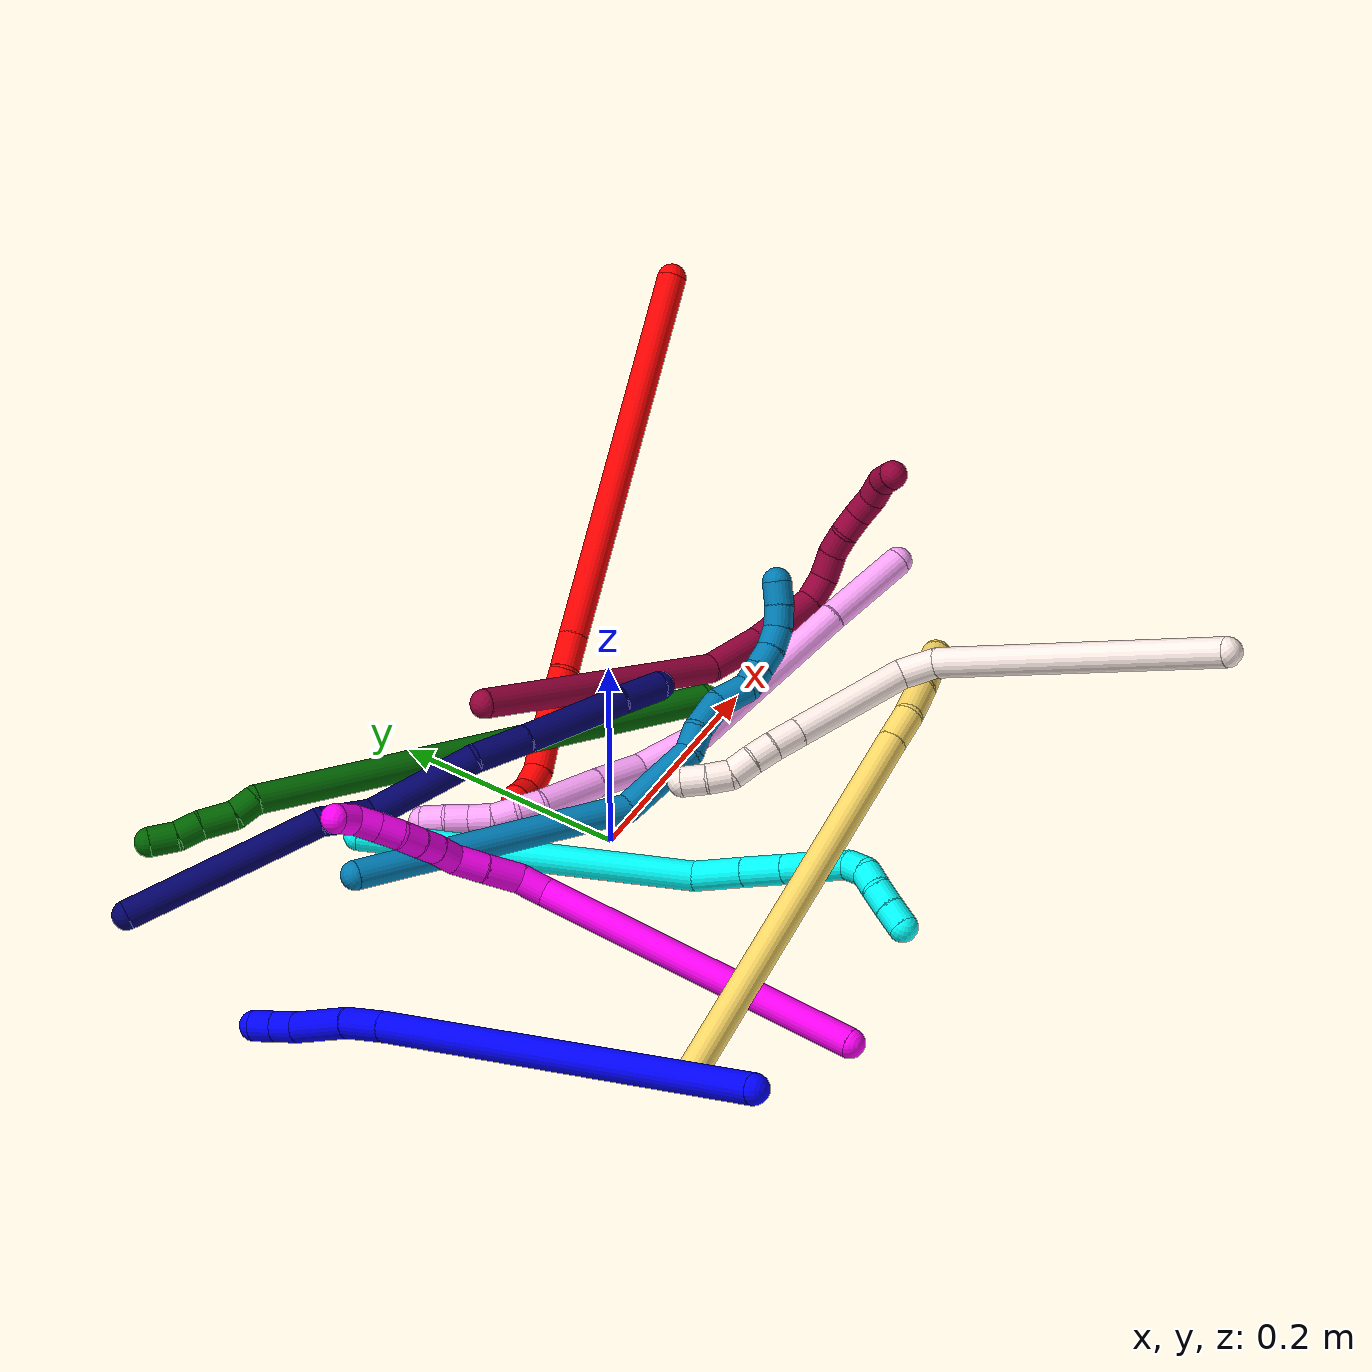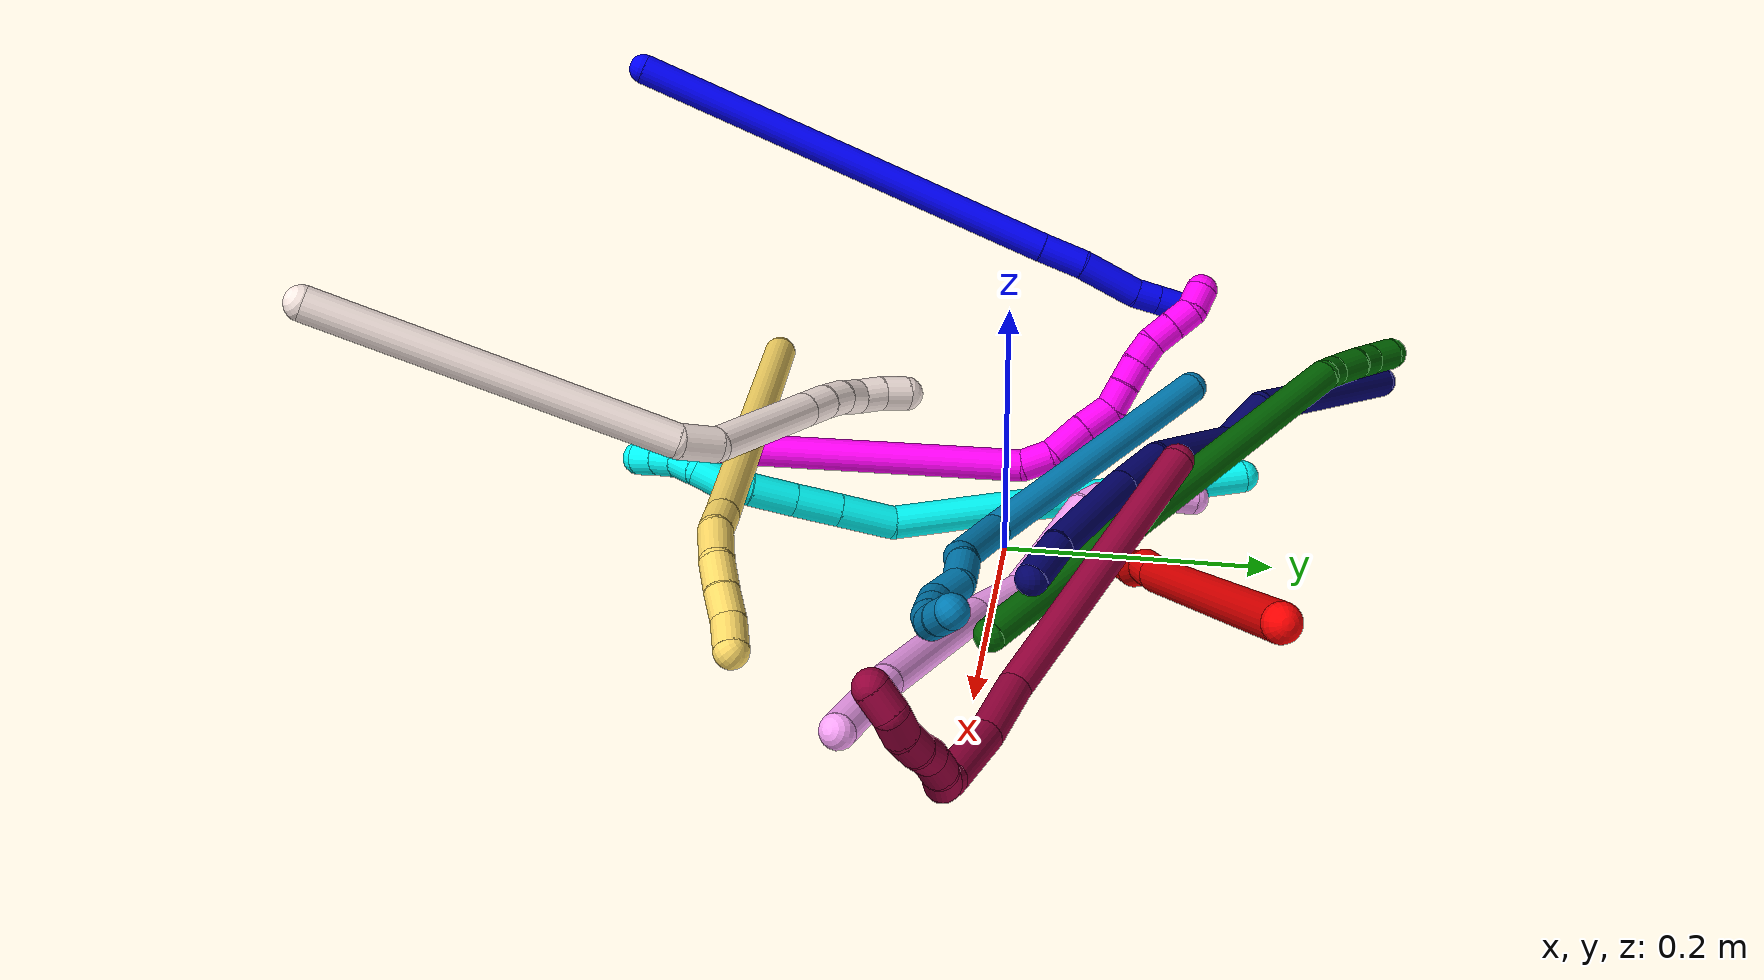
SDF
<sdf version="1.7">
 <world name="default">
  <plugin name="TubeGeneratorPlugin" filename="libtube_generator_plugin.so"/>
  <model name="photoneo_s_sensor">
   <static>1</static>
   <pose>0 0 2 1.57079 1.57079 3.14159</pose>
   <link name="link">
    <inertial><mass>0.1</mass></inertial>
    <sensor name="sensor" type="depth">
     <update_rate>30</update_rate>
     <camera>
      <horizontal_fov>1.22</horizontal_fov>
      <image><width>1920</width><height>1200</height><format>B8G8R8</format></image>
      <clip><near>0.1</near><far>4</far></clip>
      <depth_camera><output>points</output></depth_camera>
     </camera>
     <plugin name="camera_plugin" filename="libgazebo_ros_depth_camera.so">
      <baseline>0.2</baseline>
      <alwaysOn>1</alwaysOn>
      <updateRate>0.0</updateRate>
      <cameraName>camera_ir</cameraName>
      <imageTopicName>/camera/color/image_raw</imageTopicName>
      <cameraInfoTopicName>/camera/color/camera_info</cameraInfoTopicName>
      <depthImageTopicName>/camera/depth/image_raw</depthImageTopicName>
      <depthImageCameraInfoTopicName>/camera/depth/camera_info</depthImageCameraInfoTopicName>
      <pointCloudTopicName>/camera/depth/points</pointCloudTopicName>
      <frameName>fr_optical</frameName>
      <pointCloudCutoff>0.1</pointCloudCutoff>
      <pointCloudCutoffMax>2.0</pointCloudCutoffMax>
      <distortionK1>0</distortionK1>
      <distortionK2>0</distortionK2>
      <distortionK3>0</distortionK3>
      <distortionT1>0</distortionT1>
      <distortionT2>0</distortionT2>
      <CxPrime>0</CxPrime>
      <Cx>0</Cx>
      <Cy>0</Cy>
      <focalLength>0</focalLength>
      <hackBaseline>0</hackBaseline>
     </plugin>
    </sensor>
   </link>
  </model>
  <gravity>0 0 -9.8</gravity>
  <magnetic_field>6e-06 2.3e-05 -4.2e-05</magnetic_field>
  <atmosphere type="adiabatic"/>
  <physics name="default_physics" default="0" type="ode">
   <max_step_size>0.003</max_step_size>
   <real_time_factor>1</real_time_factor>
   <real_time_update_rate>1000</real_time_update_rate>
   <max_contacts>10000</max_contacts>
   <ode>
    <solver>
     <type>quick</type>
     <iters>100</iters>
     <sor>1.3</sor>
     <use_dynamic_moi_rescaling>0</use_dynamic_moi_rescaling>
    </solver>
    <constraints>
     <contact_max_correcting_vel>0</contact_max_correcting_vel>
     <contact_surface_layer>0.001</contact_surface_layer>
     <cfm>0</cfm>
     <erp>0.2</erp>
    </constraints>
   </ode>
  </physics>
  <scene><ambient>0.4 0.4 0.4 1</ambient><background>0.7 0.7 0.7 1</background><shadows>0</shadows></scene>
  <audio><device>default</device></audio>
  <spherical_coordinates>
   <surface_model>EARTH_WGS84</surface_model>
   <latitude_deg>0</latitude_deg>
   <longitude_deg>0</longitude_deg>
   <elevation>0</elevation>
   <heading_deg>0</heading_deg>
  </spherical_coordinates>
  <model name="bin">
   <static>1</static>
   <link name="bottom">
    <collision name="collision-bottom">
     <pose>0 0 -0.01 0 -0 0</pose>
     <geometry><box><size>0.8 0.6 0.02</size></box></geometry>
     <surface>
      <friction><ode><mu>100</mu><mu2>100</mu2></ode></friction>
      <contact><collide_bitmask>65535</collide_bitmask></contact>
     </surface>
    </collision>
   </link>
   <link name="west_wall">
    <collision name="collision-west_wall">
     <pose>-0.41 0 0.1 0 -0 0</pose>
     <geometry><box><size>0.02 0.6 0.2</size></box></geometry>
     <surface>
      <friction><ode><mu>100</mu><mu2>100</mu2></ode></friction>
      <contact><collide_bitmask>65535</collide_bitmask></contact>
     </surface>
    </collision>
   </link>
   <link name="east_wall">
    <collision name="collision-east_wall">
     <pose>0.41 0 0.1 0 -0 0</pose>
     <geometry><box><size>0.02 0.6 0.2</size></box></geometry>
     <surface>
      <friction><ode><mu>100</mu><mu2>100</mu2></ode></friction>
      <contact><collide_bitmask>65535</collide_bitmask></contact>
     </surface>
    </collision>
   </link>
   <link name="south_wall">
    <collision name="collision-south_wall">
     <pose>0 -0.31 0.1 0 -0 0</pose>
     <geometry><box><size>0.8 0.02 0.2</size></box></geometry>
     <surface>
      <friction><ode><mu>100</mu><mu2>100</mu2></ode></friction>
      <contact><collide_bitmask>65535</collide_bitmask></contact>
     </surface>
    </collision>
   </link>
   <link name="north_wall">
    <collision name="collision-north_wall">
     <pose>0 0.31 0.1 0 -0 0</pose>
     <geometry><box><size>0.8 0.02 0.2</size></box></geometry>
     <surface>
      <friction><ode><mu>100</mu><mu2>100</mu2></ode></friction>
      <contact><collide_bitmask>65535</collide_bitmask></contact>
     </surface>
    </collision>
   </link>
  </model>
  <model name="1">
   <static>0</static>
   <link name="1">
    <collision name="collision-cylinder-e_1_1_4">
     <pose>-0.01141 0.01002 -0.184015 -3.08719 -0.061836 1.69867</pose>
     <geometry><cylinder><radius>0.0125</radius><length>0.36928</length></cylinder></geometry>
     <surface>
      <friction><ode><mu>1.16</mu><mu2>1.16</mu2><slip1>0</slip1><slip2>0</slip2></ode></friction>
      <contact><ode><kp>1e+06</kp><kd>1</kd><max_vel>0</max_vel><min_depth>0.001</min_depth></ode></contact>
     </surface>
    </collision>
    <visual name="visual-cylinder-e_1_1_4">
     <pose>-0.01141 0.01002 -0.184015 -3.08719 -0.061836 1.69867</pose>
     <geometry><cylinder><radius>0.0125</radius><length>0.36928</length></cylinder></geometry>
     <material><ambient>0 0 1 1</ambient></material>
    </visual>
    <collision name="collision-cylinder-e_2_4_5">
     <pose>-0.022898 0.020659 -0.38692 -3.10885 -0.004103 0.249349</pose>
     <geometry><cylinder><radius>0.0125</radius><length>0.037802</length></cylinder></geometry>
     <surface>
      <friction><ode><mu>1.16</mu><mu2>1.16</mu2><slip1>0</slip1><slip2>0</slip2></ode></friction>
      <contact><ode><kp>1e+06</kp><kd>1</kd><max_vel>0</max_vel><min_depth>0.001</min_depth></ode></contact>
     </surface>
    </collision>
    <visual name="visual-cylinder-e_2_4_5">
     <pose>-0.022898 0.020659 -0.38692 -3.10885 -0.004103 0.249349</pose>
     <geometry><cylinder><radius>0.0125</radius><length>0.037802</length></cylinder></geometry>
     <material><ambient>0 0 1 1</ambient></material>
    </visual>
    <collision name="collision-cylinder-e_3_5_6">
     <pose>-0.020121 0.025031 -0.43169 -2.99754 0.108734 -1.29242</pose>
     <geometry><cylinder><radius>0.0125</radius><length>0.052611</length></cylinder></geometry>
     <surface>
      <friction><ode><mu>1.16</mu><mu2>1.16</mu2><slip1>0</slip1><slip2>0</slip2></ode></friction>
      <contact><ode><kp>1e+06</kp><kd>1</kd><max_vel>0</max_vel><min_depth>0.001</min_depth></ode></contact>
     </surface>
    </collision>
    <visual name="visual-cylinder-e_3_5_6">
     <pose>-0.020121 0.025031 -0.43169 -2.99754 0.108734 -1.29242</pose>
     <geometry><cylinder><radius>0.0125</radius><length>0.052611</length></cylinder></geometry>
     <material><ambient>0 0 1 1</ambient></material>
    </visual>
    <collision name="collision-cylinder-e_4_6_7">
     <pose>-0.016154 0.028257 -0.467604 3.08901 0.110196 2.25176</pose>
     <geometry><cylinder><radius>0.0125</radius><length>0.02022</length></cylinder></geometry>
     <surface>
      <friction><ode><mu>1.16</mu><mu2>1.16</mu2><slip1>0</slip1><slip2>0</slip2></ode></friction>
      <contact><ode><kp>1e+06</kp><kd>1</kd><max_vel>0</max_vel><min_depth>0.001</min_depth></ode></contact>
     </surface>
    </collision>
    <visual name="visual-cylinder-e_4_6_7">
     <pose>-0.016154 0.028257 -0.467604 3.08901 0.110196 2.25176</pose>
     <geometry><cylinder><radius>0.0125</radius><length>0.02022</length></cylinder></geometry>
     <material><ambient>0 0 1 1</ambient></material>
    </visual>
    <collision name="collision-cylinder-e_5_7_2">
     <pose>-0.01394 0.027205 -0.487608 3.0891 0.109984 2.25162</pose>
     <geometry><cylinder><radius>0.0125</radius><length>0.020086</length></cylinder></geometry>
     <surface>
      <friction><ode><mu>1.16</mu><mu2>1.16</mu2><slip1>0</slip1><slip2>0</slip2></ode></friction>
      <contact><ode><kp>1e+06</kp><kd>1</kd><max_vel>0</max_vel><min_depth>0.001</min_depth></ode></contact>
     </surface>
    </collision>
    <visual name="visual-cylinder-e_5_7_2">
     <pose>-0.01394 0.027205 -0.487608 3.0891 0.109984 2.25162</pose>
     <geometry><cylinder><radius>0.0125</radius><length>0.020086</length></cylinder></geometry>
     <material><ambient>0 0 1 1</ambient></material>
    </visual>
    <collision name="collision-sphere-2">
     <pose>-0.012838 0.026682 -0.497577 0 -0 0</pose>
     <geometry><sphere><radius>0.0125</radius></sphere></geometry>
     <surface>
      <friction><ode><mu>1.16</mu><mu2>1.16</mu2><slip1>0</slip1><slip2>0</slip2></ode></friction>
      <contact><ode><kp>1e+06</kp><kd>1</kd><max_vel>0</max_vel><min_depth>0.001</min_depth></ode></contact>
     </surface>
    </collision>
    <visual name="visual-sphere-2">
     <pose>-0.012838 0.026682 -0.497577 0 -0 0</pose>
     <geometry><sphere><radius>0.0125</radius></sphere></geometry>
     <material><ambient>0 0 1 1</ambient></material>
    </visual>
    <collision name="collision-sphere-7">
     <pose>-0.015043 0.027729 -0.477639 0 -0 0</pose>
     <geometry><sphere><radius>0.0125</radius></sphere></geometry>
     <surface>
      <friction><ode><mu>1.16</mu><mu2>1.16</mu2><slip1>0</slip1><slip2>0</slip2></ode></friction>
      <contact><ode><kp>1e+06</kp><kd>1</kd><max_vel>0</max_vel><min_depth>0.001</min_depth></ode></contact>
     </surface>
    </collision>
    <visual name="visual-sphere-7">
     <pose>-0.015043 0.027729 -0.477639 0 -0 0</pose>
     <geometry><sphere><radius>0.0125</radius></sphere></geometry>
     <material><ambient>0 0 1 1</ambient></material>
    </visual>
    <collision name="collision-sphere-6">
     <pose>-0.017266 0.028786 -0.457569 0 -0 0</pose>
     <geometry><sphere><radius>0.0125</radius></sphere></geometry>
     <surface>
      <friction><ode><mu>1.16</mu><mu2>1.16</mu2><slip1>0</slip1><slip2>0</slip2></ode></friction>
      <contact><ode><kp>1e+06</kp><kd>1</kd><max_vel>0</max_vel><min_depth>0.001</min_depth></ode></contact>
     </surface>
    </collision>
    <visual name="visual-sphere-6">
     <pose>-0.017266 0.028786 -0.457569 0 -0 0</pose>
     <geometry><sphere><radius>0.0125</radius></sphere></geometry>
     <material><ambient>0 0 1 1</ambient></material>
    </visual>
    <collision name="collision-sphere-5">
     <pose>-0.022976 0.021277 -0.405811 0 -0 0</pose>
     <geometry><sphere><radius>0.0125</radius></sphere></geometry>
     <surface>
      <friction><ode><mu>1.16</mu><mu2>1.16</mu2><slip1>0</slip1><slip2>0</slip2></ode></friction>
      <contact><ode><kp>1e+06</kp><kd>1</kd><max_vel>0</max_vel><min_depth>0.001</min_depth></ode></contact>
     </surface>
    </collision>
    <visual name="visual-sphere-5">
     <pose>-0.022976 0.021277 -0.405811 0 -0 0</pose>
     <geometry><sphere><radius>0.0125</radius></sphere></geometry>
     <material><ambient>0 0 1 1</ambient></material>
    </visual>
    <collision name="collision-sphere-1">
     <geometry><sphere><radius>0.0125</radius></sphere></geometry>
     <surface>
      <friction><ode><mu>1.16</mu><mu2>1.16</mu2><slip1>0</slip1><slip2>0</slip2></ode></friction>
      <contact><ode><kp>1e+06</kp><kd>1</kd><max_vel>0</max_vel><min_depth>0.001</min_depth></ode></contact>
     </surface>
    </collision>
    <visual name="visual-sphere-1">
     <geometry><sphere><radius>0.0125</radius></sphere></geometry>
     <material><ambient>0 0 1 1</ambient></material>
    </visual>
    <collision name="collision-sphere-4">
     <pose>-0.02282 0.02004 -0.368029 0 -0 0</pose>
     <geometry><sphere><radius>0.0125</radius></sphere></geometry>
     <surface>
      <friction><ode><mu>1.16</mu><mu2>1.16</mu2><slip1>0</slip1><slip2>0</slip2></ode></friction>
      <contact><ode><kp>1e+06</kp><kd>1</kd><max_vel>0</max_vel><min_depth>0.001</min_depth></ode></contact>
     </surface>
    </collision>
    <visual name="visual-sphere-4">
     <pose>-0.02282 0.02004 -0.368029 0 -0 0</pose>
     <geometry><sphere><radius>0.0125</radius></sphere></geometry>
     <material><ambient>0 0 1 1</ambient></material>
    </visual>
    <inertial>
     <pose>-0.013489 0.013832 -0.249081 0 -0 0</pose>
     <mass>0.5</mass>
     <inertia>
      <ixx>0.00363</ixx>
      <ixy>0</ixy>
      <ixz>0</ixz>
      <iyy>0.004704</iyy>
      <iyz>0</iyz>
      <izz>-1.1e-05</izz>
     </inertia>
    </inertial>
   </link>
   <pose>-0.348567 -0.34777 0.232292 -1.19494 0.306892 -2.96818</pose>
  </model>
  <model name="2">
   <static>0</static>
   <link name="2">
    <collision name="collision-cylinder-e_1_1_4">
     <pose>-0.010719 0.005513 -0.166262 -3.10844 -0.064348 2.19041</pose>
     <geometry><cylinder><radius>0.0125</radius><length>0.333398</length></cylinder></geometry>
     <surface>
      <friction><ode><mu>1.16</mu><mu2>1.16</mu2><slip1>0</slip1><slip2>0</slip2></ode></friction>
      <contact><ode><kp>1e+06</kp><kd>1</kd><max_vel>0</max_vel><min_depth>0.001</min_depth></ode></contact>
     </surface>
    </collision>
    <visual name="visual-cylinder-e_1_1_4">
     <pose>-0.010719 0.005513 -0.166262 -3.10844 -0.064348 2.19041</pose>
     <geometry><cylinder><radius>0.0125</radius><length>0.333398</length></cylinder></geometry>
     <material><ambient>1 0 0 1</ambient></material>
    </visual>
    <collision name="collision-cylinder-e_2_4_5">
     <pose>-0.023229 0.009965 -0.348168 3.07379 -0.11369 -2.06669</pose>
     <geometry><cylinder><radius>0.0125</radius><length>0.031563</length></cylinder></geometry>
     <surface>
      <friction><ode><mu>1.16</mu><mu2>1.16</mu2><slip1>0</slip1><slip2>0</slip2></ode></friction>
      <contact><ode><kp>1e+06</kp><kd>1</kd><max_vel>0</max_vel><min_depth>0.001</min_depth></ode></contact>
     </surface>
    </collision>
    <visual name="visual-cylinder-e_2_4_5">
     <pose>-0.023229 0.009965 -0.348168 3.07379 -0.11369 -2.06669</pose>
     <geometry><cylinder><radius>0.0125</radius><length>0.031563</length></cylinder></geometry>
     <material><ambient>1 0 0 1</ambient></material>
    </visual>
    <collision name="collision-cylinder-e_3_5_6">
     <pose>-0.025273 0.012934 -0.389458 -2.98567 -0.009772 0.124935</pose>
     <geometry><cylinder><radius>0.0125</radius><length>0.051925</length></cylinder></geometry>
     <surface>
      <friction><ode><mu>1.16</mu><mu2>1.16</mu2><slip1>0</slip1><slip2>0</slip2></ode></friction>
      <contact><ode><kp>1e+06</kp><kd>1</kd><max_vel>0</max_vel><min_depth>0.001</min_depth></ode></contact>
     </surface>
    </collision>
    <visual name="visual-cylinder-e_3_5_6">
     <pose>-0.025273 0.012934 -0.389458 -2.98567 -0.009772 0.124935</pose>
     <geometry><cylinder><radius>0.0125</radius><length>0.051925</length></cylinder></geometry>
     <material><ambient>1 0 0 1</ambient></material>
    </visual>
    <collision name="collision-cylinder-e_4_6_7">
     <pose>-0.027399 0.014507 -0.434867 3.01783 -0.093758 -1.29612</pose>
     <geometry><cylinder><radius>0.0125</radius><length>0.040006</length></cylinder></geometry>
     <surface>
      <friction><ode><mu>1.16</mu><mu2>1.16</mu2><slip1>0</slip1><slip2>0</slip2></ode></friction>
      <contact><ode><kp>1e+06</kp><kd>1</kd><max_vel>0</max_vel><min_depth>0.001</min_depth></ode></contact>
     </surface>
    </collision>
    <visual name="visual-cylinder-e_4_6_7">
     <pose>-0.027399 0.014507 -0.434867 3.01783 -0.093758 -1.29612</pose>
     <geometry><cylinder><radius>0.0125</radius><length>0.040006</length></cylinder></geometry>
     <material><ambient>1 0 0 1</ambient></material>
    </visual>
    <collision name="collision-cylinder-e_5_7_8">
     <pose>-0.033791 0.010378 -0.464928 2.98082 -0.408717 -2.40015</pose>
     <geometry><cylinder><radius>0.0125</radius><length>0.022738</length></cylinder></geometry>
     <surface>
      <friction><ode><mu>1.16</mu><mu2>1.16</mu2><slip1>0</slip1><slip2>0</slip2></ode></friction>
      <contact><ode><kp>1e+06</kp><kd>1</kd><max_vel>0</max_vel><min_depth>0.001</min_depth></ode></contact>
     </surface>
    </collision>
    <visual name="visual-cylinder-e_5_7_8">
     <pose>-0.033791 0.010378 -0.464928 2.98082 -0.408717 -2.40015</pose>
     <geometry><cylinder><radius>0.0125</radius><length>0.022738</length></cylinder></geometry>
     <material><ambient>1 0 0 1</ambient></material>
    </visual>
    <collision name="collision-cylinder-e_6_8_2">
     <pose>-0.045327 0.004452 -0.481257 2.527 -0.760113 -1.79894</pose>
     <geometry><cylinder><radius>0.0125</radius><length>0.02037</length></cylinder></geometry>
     <surface>
      <friction><ode><mu>1.16</mu><mu2>1.16</mu2><slip1>0</slip1><slip2>0</slip2></ode></friction>
      <contact><ode><kp>1e+06</kp><kd>1</kd><max_vel>0</max_vel><min_depth>0.001</min_depth></ode></contact>
     </surface>
    </collision>
    <visual name="visual-cylinder-e_6_8_2">
     <pose>-0.045327 0.004452 -0.481257 2.527 -0.760113 -1.79894</pose>
     <geometry><cylinder><radius>0.0125</radius><length>0.02037</length></cylinder></geometry>
     <material><ambient>1 0 0 1</ambient></material>
    </visual>
    <collision name="collision-sphere-2">
     <pose>-0.052344 0.000195 -0.487288 0 -0 0</pose>
     <geometry><sphere><radius>0.0125</radius></sphere></geometry>
     <surface>
      <friction><ode><mu>1.16</mu><mu2>1.16</mu2><slip1>0</slip1><slip2>0</slip2></ode></friction>
      <contact><ode><kp>1e+06</kp><kd>1</kd><max_vel>0</max_vel><min_depth>0.001</min_depth></ode></contact>
     </surface>
    </collision>
    <visual name="visual-sphere-2">
     <pose>-0.052344 0.000195 -0.487288 0 -0 0</pose>
     <geometry><sphere><radius>0.0125</radius></sphere></geometry>
     <material><ambient>1 0 0 1</ambient></material>
    </visual>
    <collision name="collision-sphere-4">
     <pose>-0.021439 0.011027 -0.332525 0 -0 0</pose>
     <geometry><sphere><radius>0.0125</radius></sphere></geometry>
     <surface>
      <friction><ode><mu>1.16</mu><mu2>1.16</mu2><slip1>0</slip1><slip2>0</slip2></ode></friction>
      <contact><ode><kp>1e+06</kp><kd>1</kd><max_vel>0</max_vel><min_depth>0.001</min_depth></ode></contact>
     </surface>
    </collision>
    <visual name="visual-sphere-4">
     <pose>-0.021439 0.011027 -0.332525 0 -0 0</pose>
     <geometry><sphere><radius>0.0125</radius></sphere></geometry>
     <material><ambient>1 0 0 1</ambient></material>
    </visual>
    <collision name="collision-sphere-1">
     <geometry><sphere><radius>0.0125</radius></sphere></geometry>
     <surface>
      <friction><ode><mu>1.16</mu><mu2>1.16</mu2><slip1>0</slip1><slip2>0</slip2></ode></friction>
      <contact><ode><kp>1e+06</kp><kd>1</kd><max_vel>0</max_vel><min_depth>0.001</min_depth></ode></contact>
     </surface>
    </collision>
    <visual name="visual-sphere-1">
     <geometry><sphere><radius>0.0125</radius></sphere></geometry>
     <material><ambient>1 0 0 1</ambient></material>
    </visual>
    <collision name="collision-sphere-8">
     <pose>-0.038309 0.008708 -0.475227 0 -0 0</pose>
     <geometry><sphere><radius>0.0125</radius></sphere></geometry>
     <surface>
      <friction><ode><mu>1.16</mu><mu2>1.16</mu2><slip1>0</slip1><slip2>0</slip2></ode></friction>
      <contact><ode><kp>1e+06</kp><kd>1</kd><max_vel>0</max_vel><min_depth>0.001</min_depth></ode></contact>
     </surface>
    </collision>
    <visual name="visual-sphere-8">
     <pose>-0.038309 0.008708 -0.475227 0 -0 0</pose>
     <geometry><sphere><radius>0.0125</radius></sphere></geometry>
     <material><ambient>1 0 0 1</ambient></material>
    </visual>
    <collision name="collision-sphere-5">
     <pose>-0.025019 0.008902 -0.363812 0 -0 0</pose>
     <geometry><sphere><radius>0.0125</radius></sphere></geometry>
     <surface>
      <friction><ode><mu>1.16</mu><mu2>1.16</mu2><slip1>0</slip1><slip2>0</slip2></ode></friction>
      <contact><ode><kp>1e+06</kp><kd>1</kd><max_vel>0</max_vel><min_depth>0.001</min_depth></ode></contact>
     </surface>
    </collision>
    <visual name="visual-sphere-5">
     <pose>-0.025019 0.008902 -0.363812 0 -0 0</pose>
     <geometry><sphere><radius>0.0125</radius></sphere></geometry>
     <material><ambient>1 0 0 1</ambient></material>
    </visual>
    <collision name="collision-sphere-6">
     <pose>-0.025527 0.016965 -0.415104 0 -0 0</pose>
     <geometry><sphere><radius>0.0125</radius></sphere></geometry>
     <surface>
      <friction><ode><mu>1.16</mu><mu2>1.16</mu2><slip1>0</slip1><slip2>0</slip2></ode></friction>
      <contact><ode><kp>1e+06</kp><kd>1</kd><max_vel>0</max_vel><min_depth>0.001</min_depth></ode></contact>
     </surface>
    </collision>
    <visual name="visual-sphere-6">
     <pose>-0.025527 0.016965 -0.415104 0 -0 0</pose>
     <geometry><sphere><radius>0.0125</radius></sphere></geometry>
     <material><ambient>1 0 0 1</ambient></material>
    </visual>
    <collision name="collision-sphere-7">
     <pose>-0.029272 0.012048 -0.45463 0 -0 0</pose>
     <geometry><sphere><radius>0.0125</radius></sphere></geometry>
     <surface>
      <friction><ode><mu>1.16</mu><mu2>1.16</mu2><slip1>0</slip1><slip2>0</slip2></ode></friction>
      <contact><ode><kp>1e+06</kp><kd>1</kd><max_vel>0</max_vel><min_depth>0.001</min_depth></ode></contact>
     </surface>
    </collision>
    <visual name="visual-sphere-7">
     <pose>-0.029272 0.012048 -0.45463 0 -0 0</pose>
     <geometry><sphere><radius>0.0125</radius></sphere></geometry>
     <material><ambient>1 0 0 1</ambient></material>
    </visual>
    <inertial>
     <pose>-0.016814 0.007463 -0.248831 0 -0 0</pose>
     <mass>0.5</mass>
     <inertia><ixx>0.00072</ixx><ixy>0</ixy><ixz>0</ixz><iyy>0.004303</iyy><iyz>0</iyz><izz>6.2e-05</izz></inertia>
    </inertial>
   </link>
   <pose>0.414965 0.198597 0.221125 -0.946595 0.619431 -0.823257</pose>
  </model>
  <model name="3">
   <static>0</static>
   <link name="3">
    <collision name="collision-cylinder-e_1_1_4">
     <pose>-0.033392 -0.132404 -0.034888 1.82843 -0.239206 -0.309397</pose>
     <geometry><cylinder><radius>0.0125</radius><length>0.281873</length></cylinder></geometry>
     <surface>
      <friction><ode><mu>1.16</mu><mu2>1.16</mu2><slip1>0</slip1><slip2>0</slip2></ode></friction>
      <contact><ode><kp>1e+06</kp><kd>1</kd><max_vel>0</max_vel><min_depth>0.001</min_depth></ode></contact>
     </surface>
    </collision>
    <visual name="visual-cylinder-e_1_1_4">
     <pose>-0.033392 -0.132404 -0.034888 1.82843 -0.239206 -0.309397</pose>
     <geometry><cylinder><radius>0.0125</radius><length>0.281873</length></cylinder></geometry>
     <material><ambient>0.003922 1 0.996078 1</ambient></material>
    </visual>
    <collision name="collision-cylinder-e_2_4_5">
     <pose>-0.07025 -0.282733 -0.082546 2.18987 -0.156198 -0.301397</pose>
     <geometry><cylinder><radius>0.0125</radius><length>0.044558</length></cylinder></geometry>
     <surface>
      <friction><ode><mu>1.16</mu><mu2>1.16</mu2><slip1>0</slip1><slip2>0</slip2></ode></friction>
      <contact><ode><kp>1e+06</kp><kd>1</kd><max_vel>0</max_vel><min_depth>0.001</min_depth></ode></contact>
     </surface>
    </collision>
    <visual name="visual-cylinder-e_2_4_5">
     <pose>-0.07025 -0.282733 -0.082546 2.18987 -0.156198 -0.301397</pose>
     <geometry><cylinder><radius>0.0125</radius><length>0.044558</length></cylinder></geometry>
     <material><ambient>0.003922 1 0.996078 1</ambient></material>
    </visual>
    <collision name="collision-cylinder-e_3_5_6">
     <pose>-0.07642 -0.315181 -0.10546 2.18041 -0.15146 -0.289036</pose>
     <geometry><cylinder><radius>0.0125</radius><length>0.035842</length></cylinder></geometry>
     <surface>
      <friction><ode><mu>1.16</mu><mu2>1.16</mu2><slip1>0</slip1><slip2>0</slip2></ode></friction>
      <contact><ode><kp>1e+06</kp><kd>1</kd><max_vel>0</max_vel><min_depth>0.001</min_depth></ode></contact>
     </surface>
    </collision>
    <visual name="visual-cylinder-e_3_5_6">
     <pose>-0.07642 -0.315181 -0.10546 2.18041 -0.15146 -0.289036</pose>
     <geometry><cylinder><radius>0.0125</radius><length>0.035842</length></cylinder></geometry>
     <material><ambient>0.003922 1 0.996078 1</ambient></material>
    </visual>
    <collision name="collision-cylinder-e_4_6_7">
     <pose>-0.08184 -0.34375 -0.125818 2.19962 -0.155106 -0.302876</pose>
     <geometry><cylinder><radius>0.0125</radius><length>0.035156</length></cylinder></geometry>
     <surface>
      <friction><ode><mu>1.16</mu><mu2>1.16</mu2><slip1>0</slip1><slip2>0</slip2></ode></friction>
      <contact><ode><kp>1e+06</kp><kd>1</kd><max_vel>0</max_vel><min_depth>0.001</min_depth></ode></contact>
     </surface>
    </collision>
    <visual name="visual-cylinder-e_4_6_7">
     <pose>-0.08184 -0.34375 -0.125818 2.19962 -0.155106 -0.302876</pose>
     <geometry><cylinder><radius>0.0125</radius><length>0.035156</length></cylinder></geometry>
     <material><ambient>0.003922 1 0.996078 1</ambient></material>
    </visual>
    <collision name="collision-cylinder-e_5_7_8">
     <pose>-0.085584 -0.366861 -0.142355 2.17975 -0.092849 -0.177605</pose>
     <geometry><cylinder><radius>0.0125</radius><length>0.0222</length></cylinder></geometry>
     <surface>
      <friction><ode><mu>1.16</mu><mu2>1.16</mu2><slip1>0</slip1><slip2>0</slip2></ode></friction>
      <contact><ode><kp>1e+06</kp><kd>1</kd><max_vel>0</max_vel><min_depth>0.001</min_depth></ode></contact>
     </surface>
    </collision>
    <visual name="visual-cylinder-e_5_7_8">
     <pose>-0.085584 -0.366861 -0.142355 2.17975 -0.092849 -0.177605</pose>
     <geometry><cylinder><radius>0.0125</radius><length>0.0222</length></cylinder></geometry>
     <material><ambient>0.003922 1 0.996078 1</ambient></material>
    </visual>
    <collision name="collision-cylinder-e_6_8_9">
     <pose>-0.083007 -0.383644 -0.154018 2.17617 0.366903 0.680534</pose>
     <geometry><cylinder><radius>0.0125</radius><length>0.020108</length></cylinder></geometry>
     <surface>
      <friction><ode><mu>1.16</mu><mu2>1.16</mu2><slip1>0</slip1><slip2>0</slip2></ode></friction>
      <contact><ode><kp>1e+06</kp><kd>1</kd><max_vel>0</max_vel><min_depth>0.001</min_depth></ode></contact>
     </surface>
    </collision>
    <visual name="visual-cylinder-e_6_8_9">
     <pose>-0.083007 -0.383644 -0.154018 2.17617 0.366903 0.680534</pose>
     <geometry><cylinder><radius>0.0125</radius><length>0.020108</length></cylinder></geometry>
     <material><ambient>0.003922 1 0.996078 1</ambient></material>
    </visual>
    <collision name="collision-cylinder-e_7_9_10">
     <pose>-0.07247 -0.398434 -0.161305 1.83931 0.756946 0.961929</pose>
     <geometry><cylinder><radius>0.0125</radius><length>0.020184</length></cylinder></geometry>
     <surface>
      <friction><ode><mu>1.16</mu><mu2>1.16</mu2><slip1>0</slip1><slip2>0</slip2></ode></friction>
      <contact><ode><kp>1e+06</kp><kd>1</kd><max_vel>0</max_vel><min_depth>0.001</min_depth></ode></contact>
     </surface>
    </collision>
    <visual name="visual-cylinder-e_7_9_10">
     <pose>-0.07247 -0.398434 -0.161305 1.83931 0.756946 0.961929</pose>
     <geometry><cylinder><radius>0.0125</radius><length>0.020184</length></cylinder></geometry>
     <material><ambient>0.003922 1 0.996078 1</ambient></material>
    </visual>
    <collision name="collision-cylinder-e_8_10_11">
     <pose>-0.059796 -0.413699 -0.163163 1.56005 0.611522 0.605382</pose>
     <geometry><cylinder><radius>0.0125</radius><length>0.020009</length></cylinder></geometry>
     <surface>
      <friction><ode><mu>1.16</mu><mu2>1.16</mu2><slip1>0</slip1><slip2>0</slip2></ode></friction>
      <contact><ode><kp>1e+06</kp><kd>1</kd><max_vel>0</max_vel><min_depth>0.001</min_depth></ode></contact>
     </surface>
    </collision>
    <visual name="visual-cylinder-e_8_10_11">
     <pose>-0.059796 -0.413699 -0.163163 1.56005 0.611522 0.605382</pose>
     <geometry><cylinder><radius>0.0125</radius><length>0.020009</length></cylinder></geometry>
     <material><ambient>0.003922 1 0.996078 1</ambient></material>
    </visual>
    <collision name="collision-cylinder-e_9_11_2">
     <pose>-0.048633 -0.430326 -0.162681 1.52411 0.570515 0.545781</pose>
     <geometry><cylinder><radius>0.0125</radius><length>0.020069</length></cylinder></geometry>
     <surface>
      <friction><ode><mu>1.16</mu><mu2>1.16</mu2><slip1>0</slip1><slip2>0</slip2></ode></friction>
      <contact><ode><kp>1e+06</kp><kd>1</kd><max_vel>0</max_vel><min_depth>0.001</min_depth></ode></contact>
     </surface>
    </collision>
    <visual name="visual-cylinder-e_9_11_2">
     <pose>-0.048633 -0.430326 -0.162681 1.52411 0.570515 0.545781</pose>
     <geometry><cylinder><radius>0.0125</radius><length>0.020069</length></cylinder></geometry>
     <material><ambient>0.003922 1 0.996078 1</ambient></material>
    </visual>
    <collision name="collision-sphere-2">
     <pose>-0.043214 -0.438762 -0.162287 0 -0 0</pose>
     <geometry><sphere><radius>0.0125</radius></sphere></geometry>
     <surface>
      <friction><ode><mu>1.16</mu><mu2>1.16</mu2><slip1>0</slip1><slip2>0</slip2></ode></friction>
      <contact><ode><kp>1e+06</kp><kd>1</kd><max_vel>0</max_vel><min_depth>0.001</min_depth></ode></contact>
     </surface>
    </collision>
    <visual name="visual-sphere-2">
     <pose>-0.043214 -0.438762 -0.162287 0 -0 0</pose>
     <geometry><sphere><radius>0.0125</radius></sphere></geometry>
     <material><ambient>0.003922 1 0.996078 1</ambient></material>
    </visual>
    <collision name="collision-sphere-11">
     <pose>-0.054052 -0.42189 -0.163075 0 -0 0</pose>
     <geometry><sphere><radius>0.0125</radius></sphere></geometry>
     <surface>
      <friction><ode><mu>1.16</mu><mu2>1.16</mu2><slip1>0</slip1><slip2>0</slip2></ode></friction>
      <contact><ode><kp>1e+06</kp><kd>1</kd><max_vel>0</max_vel><min_depth>0.001</min_depth></ode></contact>
     </surface>
    </collision>
    <visual name="visual-sphere-11">
     <pose>-0.054052 -0.42189 -0.163075 0 -0 0</pose>
     <geometry><sphere><radius>0.0125</radius></sphere></geometry>
     <material><ambient>0.003922 1 0.996078 1</ambient></material>
    </visual>
    <collision name="collision-sphere-10">
     <pose>-0.06554 -0.405508 -0.163251 0 -0 0</pose>
     <geometry><sphere><radius>0.0125</radius></sphere></geometry>
     <surface>
      <friction><ode><mu>1.16</mu><mu2>1.16</mu2><slip1>0</slip1><slip2>0</slip2></ode></friction>
      <contact><ode><kp>1e+06</kp><kd>1</kd><max_vel>0</max_vel><min_depth>0.001</min_depth></ode></contact>
     </surface>
    </collision>
    <visual name="visual-sphere-10">
     <pose>-0.06554 -0.405508 -0.163251 0 -0 0</pose>
     <geometry><sphere><radius>0.0125</radius></sphere></geometry>
     <material><ambient>0.003922 1 0.996078 1</ambient></material>
    </visual>
    <collision name="collision-sphere-9">
     <pose>-0.0794 -0.391361 -0.159359 0 -0 0</pose>
     <geometry><sphere><radius>0.0125</radius></sphere></geometry>
     <surface>
      <friction><ode><mu>1.16</mu><mu2>1.16</mu2><slip1>0</slip1><slip2>0</slip2></ode></friction>
      <contact><ode><kp>1e+06</kp><kd>1</kd><max_vel>0</max_vel><min_depth>0.001</min_depth></ode></contact>
     </surface>
    </collision>
    <visual name="visual-sphere-9">
     <pose>-0.0794 -0.391361 -0.159359 0 -0 0</pose>
     <geometry><sphere><radius>0.0125</radius></sphere></geometry>
     <material><ambient>0.003922 1 0.996078 1</ambient></material>
    </visual>
    <collision name="collision-sphere-4">
     <pose>-0.066785 -0.264809 -0.069775 0 -0 0</pose>
     <geometry><sphere><radius>0.0125</radius></sphere></geometry>
     <surface>
      <friction><ode><mu>1.16</mu><mu2>1.16</mu2><slip1>0</slip1><slip2>0</slip2></ode></friction>
      <contact><ode><kp>1e+06</kp><kd>1</kd><max_vel>0</max_vel><min_depth>0.001</min_depth></ode></contact>
     </surface>
    </collision>
    <visual name="visual-sphere-4">
     <pose>-0.066785 -0.264809 -0.069775 0 -0 0</pose>
     <geometry><sphere><radius>0.0125</radius></sphere></geometry>
     <material><ambient>0.003922 1 0.996078 1</ambient></material>
    </visual>
    <collision name="collision-sphere-1">
     <geometry><sphere><radius>0.0125</radius></sphere></geometry>
     <surface>
      <friction><ode><mu>1.16</mu><mu2>1.16</mu2><slip1>0</slip1><slip2>0</slip2></ode></friction>
      <contact><ode><kp>1e+06</kp><kd>1</kd><max_vel>0</max_vel><min_depth>0.001</min_depth></ode></contact>
     </surface>
    </collision>
    <visual name="visual-sphere-1">
     <geometry><sphere><radius>0.0125</radius></sphere></geometry>
     <material><ambient>0.003922 1 0.996078 1</ambient></material>
    </visual>
    <collision name="collision-sphere-8">
     <pose>-0.086614 -0.375927 -0.148677 0 -0 0</pose>
     <geometry><sphere><radius>0.0125</radius></sphere></geometry>
     <surface>
      <friction><ode><mu>1.16</mu><mu2>1.16</mu2><slip1>0</slip1><slip2>0</slip2></ode></friction>
      <contact><ode><kp>1e+06</kp><kd>1</kd><max_vel>0</max_vel><min_depth>0.001</min_depth></ode></contact>
     </surface>
    </collision>
    <visual name="visual-sphere-8">
     <pose>-0.086614 -0.375927 -0.148677 0 -0 0</pose>
     <geometry><sphere><radius>0.0125</radius></sphere></geometry>
     <material><ambient>0.003922 1 0.996078 1</ambient></material>
    </visual>
    <collision name="collision-sphere-5">
     <pose>-0.073716 -0.300656 -0.095317 0 -0 0</pose>
     <geometry><sphere><radius>0.0125</radius></sphere></geometry>
     <surface>
      <friction><ode><mu>1.16</mu><mu2>1.16</mu2><slip1>0</slip1><slip2>0</slip2></ode></friction>
      <contact><ode><kp>1e+06</kp><kd>1</kd><max_vel>0</max_vel><min_depth>0.001</min_depth></ode></contact>
     </surface>
    </collision>
    <visual name="visual-sphere-5">
     <pose>-0.073716 -0.300656 -0.095317 0 -0 0</pose>
     <geometry><sphere><radius>0.0125</radius></sphere></geometry>
     <material><ambient>0.003922 1 0.996078 1</ambient></material>
    </visual>
    <collision name="collision-sphere-6">
     <pose>-0.079124 -0.329706 -0.115603 0 -0 0</pose>
     <geometry><sphere><radius>0.0125</radius></sphere></geometry>
     <surface>
      <friction><ode><mu>1.16</mu><mu2>1.16</mu2><slip1>0</slip1><slip2>0</slip2></ode></friction>
      <contact><ode><kp>1e+06</kp><kd>1</kd><max_vel>0</max_vel><min_depth>0.001</min_depth></ode></contact>
     </surface>
    </collision>
    <visual name="visual-sphere-6">
     <pose>-0.079124 -0.329706 -0.115603 0 -0 0</pose>
     <geometry><sphere><radius>0.0125</radius></sphere></geometry>
     <material><ambient>0.003922 1 0.996078 1</ambient></material>
    </visual>
    <collision name="collision-sphere-7">
     <pose>-0.084555 -0.357795 -0.136033 0 -0 0</pose>
     <geometry><sphere><radius>0.0125</radius></sphere></geometry>
     <surface>
      <friction><ode><mu>1.16</mu><mu2>1.16</mu2><slip1>0</slip1><slip2>0</slip2></ode></friction>
      <contact><ode><kp>1e+06</kp><kd>1</kd><max_vel>0</max_vel><min_depth>0.001</min_depth></ode></contact>
     </surface>
    </collision>
    <visual name="visual-sphere-7">
     <pose>-0.084555 -0.357795 -0.136033 0 -0 0</pose>
     <geometry><sphere><radius>0.0125</radius></sphere></geometry>
     <material><ambient>0.003922 1 0.996078 1</ambient></material>
    </visual>
    <inertial>
     <pose>-0.050726 -0.228231 -0.075516 0 -0 0</pose>
     <mass>0.5</mass>
     <inertia>
      <ixx>0.001199</ixx>
      <ixy>0</ixy>
      <ixz>0</ixz>
      <iyy>-0.000927</iyy>
      <iyz>0</iyz>
      <izz>0.002217</izz>
     </inertia>
    </inertial>
   </link>
   <pose>-0.114121 0.174634 0.011499 2.87841 0.022652 -2.9892</pose>
  </model>
  <model name="4">
   <static>0</static>
   <link name="4">
    <collision name="collision-cylinder-e_1_1_4">
     <pose>-0.018576 0.005208 -0.034584 -2.99214 -0.488256 2.55767</pose>
     <geometry><cylinder><radius>0.0125</radius><length>0.079202</length></cylinder></geometry>
     <surface>
      <friction><ode><mu>1.16</mu><mu2>1.16</mu2><slip1>0</slip1><slip2>0</slip2></ode></friction>
      <contact><ode><kp>1e+06</kp><kd>1</kd><max_vel>0</max_vel><min_depth>0.001</min_depth></ode></contact>
     </surface>
    </collision>
    <visual name="visual-cylinder-e_1_1_4">
     <pose>-0.018576 0.005208 -0.034584 -2.99214 -0.488256 2.55767</pose>
     <geometry><cylinder><radius>0.0125</radius><length>0.079202</length></cylinder></geometry>
     <material><ambient>1 0.65098 0.996078 1</ambient></material>
    </visual>
    <collision name="collision-cylinder-e_2_4_5">
     <pose>-0.068979 0.017455 -0.142574 -3.04599 -0.407434 2.68646</pose>
     <geometry><cylinder><radius>0.0125</radius><length>0.160635</length></cylinder></geometry>
     <surface>
      <friction><ode><mu>1.16</mu><mu2>1.16</mu2><slip1>0</slip1><slip2>0</slip2></ode></friction>
      <contact><ode><kp>1e+06</kp><kd>1</kd><max_vel>0</max_vel><min_depth>0.001</min_depth></ode></contact>
     </surface>
    </collision>
    <visual name="visual-cylinder-e_2_4_5">
     <pose>-0.068979 0.017455 -0.142574 -3.04599 -0.407434 2.68646</pose>
     <geometry><cylinder><radius>0.0125</radius><length>0.160635</length></cylinder></geometry>
     <material><ambient>1 0.65098 0.996078 1</ambient></material>
    </visual>
    <collision name="collision-cylinder-e_3_5_6">
     <pose>-0.108731 0.03296 -0.241421 -2.82036 -0.287412 1.45806</pose>
     <geometry><cylinder><radius>0.0125</radius><length>0.055918</length></cylinder></geometry>
     <surface>
      <friction><ode><mu>1.16</mu><mu2>1.16</mu2><slip1>0</slip1><slip2>0</slip2></ode></friction>
      <contact><ode><kp>1e+06</kp><kd>1</kd><max_vel>0</max_vel><min_depth>0.001</min_depth></ode></contact>
     </surface>
    </collision>
    <visual name="visual-cylinder-e_3_5_6">
     <pose>-0.108731 0.03296 -0.241421 -2.82036 -0.287412 1.45806</pose>
     <geometry><cylinder><radius>0.0125</radius><length>0.055918</length></cylinder></geometry>
     <material><ambient>1 0.65098 0.996078 1</ambient></material>
    </visual>
    <collision name="collision-cylinder-e_4_6_7">
     <pose>-0.128378 0.051735 -0.282708 -2.56477 -0.55501 1.53012</pose>
     <geometry><cylinder><radius>0.0125</radius><length>0.044487</length></cylinder></geometry>
     <surface>
      <friction><ode><mu>1.16</mu><mu2>1.16</mu2><slip1>0</slip1><slip2>0</slip2></ode></friction>
      <contact><ode><kp>1e+06</kp><kd>1</kd><max_vel>0</max_vel><min_depth>0.001</min_depth></ode></contact>
     </surface>
    </collision>
    <visual name="visual-cylinder-e_4_6_7">
     <pose>-0.128378 0.051735 -0.282708 -2.56477 -0.55501 1.53012</pose>
     <geometry><cylinder><radius>0.0125</radius><length>0.044487</length></cylinder></geometry>
     <material><ambient>1 0.65098 0.996078 1</ambient></material>
    </visual>
    <collision name="collision-cylinder-e_5_7_8">
     <pose>-0.155847 0.074719 -0.31951 -2.59766 -0.571452 1.62278</pose>
     <geometry><cylinder><radius>0.0125</radius><length>0.058234</length></cylinder></geometry>
     <surface>
      <friction><ode><mu>1.16</mu><mu2>1.16</mu2><slip1>0</slip1><slip2>0</slip2></ode></friction>
      <contact><ode><kp>1e+06</kp><kd>1</kd><max_vel>0</max_vel><min_depth>0.001</min_depth></ode></contact>
     </surface>
    </collision>
    <visual name="visual-cylinder-e_5_7_8">
     <pose>-0.155847 0.074719 -0.31951 -2.59766 -0.571452 1.62278</pose>
     <geometry><cylinder><radius>0.0125</radius><length>0.058234</length></cylinder></geometry>
     <material><ambient>1 0.65098 0.996078 1</ambient></material>
    </visual>
    <collision name="collision-cylinder-e_6_8_9">
     <pose>-0.174219 0.092537 -0.349246 -2.61163 -0.252403 0.87471</pose>
     <geometry><cylinder><radius>0.0125</radius><length>0.021017</length></cylinder></geometry>
     <surface>
      <friction><ode><mu>1.16</mu><mu2>1.16</mu2><slip1>0</slip1><slip2>0</slip2></ode></friction>
      <contact><ode><kp>1e+06</kp><kd>1</kd><max_vel>0</max_vel><min_depth>0.001</min_depth></ode></contact>
     </surface>
    </collision>
    <visual name="visual-cylinder-e_6_8_9">
     <pose>-0.174219 0.092537 -0.349246 -2.61163 -0.252403 0.87471</pose>
     <geometry><cylinder><radius>0.0125</radius><length>0.021017</length></cylinder></geometry>
     <material><ambient>1 0.65098 0.996078 1</ambient></material>
    </visual>
    <collision name="collision-cylinder-e_7_9_10">
     <pose>-0.176456 0.101836 -0.367117 -2.71293 0.038734 -0.177502</pose>
     <geometry><cylinder><radius>0.0125</radius><length>0.020006</length></cylinder></geometry>
     <surface>
      <friction><ode><mu>1.16</mu><mu2>1.16</mu2><slip1>0</slip1><slip2>0</slip2></ode></friction>
      <contact><ode><kp>1e+06</kp><kd>1</kd><max_vel>0</max_vel><min_depth>0.001</min_depth></ode></contact>
     </surface>
    </collision>
    <visual name="visual-cylinder-e_7_9_10">
     <pose>-0.176456 0.101836 -0.367117 -2.71293 0.038734 -0.177502</pose>
     <geometry><cylinder><radius>0.0125</radius><length>0.020006</length></cylinder></geometry>
     <material><ambient>1 0.65098 0.996078 1</ambient></material>
    </visual>
    <collision name="collision-cylinder-e_8_10_11">
     <pose>-0.173222 0.111621 -0.384036 -2.51804 0.287021 -0.842991</pose>
     <geometry><cylinder><radius>0.0125</radius><length>0.020109</length></cylinder></geometry>
     <surface>
      <friction><ode><mu>1.16</mu><mu2>1.16</mu2><slip1>0</slip1><slip2>0</slip2></ode></friction>
      <contact><ode><kp>1e+06</kp><kd>1</kd><max_vel>0</max_vel><min_depth>0.001</min_depth></ode></contact>
     </surface>
    </collision>
    <visual name="visual-cylinder-e_8_10_11">
     <pose>-0.173222 0.111621 -0.384036 -2.51804 0.287021 -0.842991</pose>
     <geometry><cylinder><radius>0.0125</radius><length>0.020109</length></cylinder></geometry>
     <material><ambient>1 0.65098 0.996078 1</ambient></material>
    </visual>
    <collision name="collision-cylinder-e_9_11_12">
     <pose>-0.168453 0.123456 -0.399613 -2.46639 0.191352 -0.533727</pose>
     <geometry><cylinder><radius>0.0125</radius><length>0.020222</length></cylinder></geometry>
     <surface>
      <friction><ode><mu>1.16</mu><mu2>1.16</mu2><slip1>0</slip1><slip2>0</slip2></ode></friction>
      <contact><ode><kp>1e+06</kp><kd>1</kd><max_vel>0</max_vel><min_depth>0.001</min_depth></ode></contact>
     </surface>
    </collision>
    <visual name="visual-cylinder-e_9_11_12">
     <pose>-0.168453 0.123456 -0.399613 -2.46639 0.191352 -0.533727</pose>
     <geometry><cylinder><radius>0.0125</radius><length>0.020222</length></cylinder></geometry>
     <material><ambient>1 0.65098 0.996078 1</ambient></material>
    </visual>
    <collision name="collision-cylinder-e_10_12_2">
     <pose>-0.163002 0.134851 -0.415255 -2.55995 0.357445 -1.08606</pose>
     <geometry><cylinder><radius>0.0125</radius><length>0.02017</length></cylinder></geometry>
     <surface>
      <friction><ode><mu>1.16</mu><mu2>1.16</mu2><slip1>0</slip1><slip2>0</slip2></ode></friction>
      <contact><ode><kp>1e+06</kp><kd>1</kd><max_vel>0</max_vel><min_depth>0.001</min_depth></ode></contact>
     </surface>
    </collision>
    <visual name="visual-cylinder-e_10_12_2">
     <pose>-0.163002 0.134851 -0.415255 -2.55995 0.357445 -1.08606</pose>
     <geometry><cylinder><radius>0.0125</radius><length>0.02017</length></cylinder></geometry>
     <material><ambient>1 0.65098 0.996078 1</ambient></material>
    </visual>
    <collision name="collision-sphere-2">
     <pose>-0.159473 0.140042 -0.423149 0 -0 0</pose>
     <geometry><sphere><radius>0.0125</radius></sphere></geometry>
     <surface>
      <friction><ode><mu>1.16</mu><mu2>1.16</mu2><slip1>0</slip1><slip2>0</slip2></ode></friction>
      <contact><ode><kp>1e+06</kp><kd>1</kd><max_vel>0</max_vel><min_depth>0.001</min_depth></ode></contact>
     </surface>
    </collision>
    <visual name="visual-sphere-2">
     <pose>-0.159473 0.140042 -0.423149 0 -0 0</pose>
     <geometry><sphere><radius>0.0125</radius></sphere></geometry>
     <material><ambient>1 0.65098 0.996078 1</ambient></material>
    </visual>
    <collision name="collision-sphere-12">
     <pose>-0.16653 0.129661 -0.407361 0 -0 0</pose>
     <geometry><sphere><radius>0.0125</radius></sphere></geometry>
     <surface>
      <friction><ode><mu>1.16</mu><mu2>1.16</mu2><slip1>0</slip1><slip2>0</slip2></ode></friction>
      <contact><ode><kp>1e+06</kp><kd>1</kd><max_vel>0</max_vel><min_depth>0.001</min_depth></ode></contact>
     </surface>
    </collision>
    <visual name="visual-sphere-12">
     <pose>-0.16653 0.129661 -0.407361 0 -0 0</pose>
     <geometry><sphere><radius>0.0125</radius></sphere></geometry>
     <material><ambient>1 0.65098 0.996078 1</ambient></material>
    </visual>
    <collision name="collision-sphere-11">
     <pose>-0.170376 0.117252 -0.391865 0 -0 0</pose>
     <geometry><sphere><radius>0.0125</radius></sphere></geometry>
     <surface>
      <friction><ode><mu>1.16</mu><mu2>1.16</mu2><slip1>0</slip1><slip2>0</slip2></ode></friction>
      <contact><ode><kp>1e+06</kp><kd>1</kd><max_vel>0</max_vel><min_depth>0.001</min_depth></ode></contact>
     </surface>
    </collision>
    <visual name="visual-sphere-11">
     <pose>-0.170376 0.117252 -0.391865 0 -0 0</pose>
     <geometry><sphere><radius>0.0125</radius></sphere></geometry>
     <material><ambient>1 0.65098 0.996078 1</ambient></material>
    </visual>
    <collision name="collision-sphere-10">
     <pose>-0.176069 0.10599 -0.376208 0 -0 0</pose>
     <geometry><sphere><radius>0.0125</radius></sphere></geometry>
     <surface>
      <friction><ode><mu>1.16</mu><mu2>1.16</mu2><slip1>0</slip1><slip2>0</slip2></ode></friction>
      <contact><ode><kp>1e+06</kp><kd>1</kd><max_vel>0</max_vel><min_depth>0.001</min_depth></ode></contact>
     </surface>
    </collision>
    <visual name="visual-sphere-10">
     <pose>-0.176069 0.10599 -0.376208 0 -0 0</pose>
     <geometry><sphere><radius>0.0125</radius></sphere></geometry>
     <material><ambient>1 0.65098 0.996078 1</ambient></material>
    </visual>
    <collision name="collision-sphere-9">
     <pose>-0.176844 0.097681 -0.358026 0 -0 0</pose>
     <geometry><sphere><radius>0.0125</radius></sphere></geometry>
     <surface>
      <friction><ode><mu>1.16</mu><mu2>1.16</mu2><slip1>0</slip1><slip2>0</slip2></ode></friction>
      <contact><ode><kp>1e+06</kp><kd>1</kd><max_vel>0</max_vel><min_depth>0.001</min_depth></ode></contact>
     </surface>
    </collision>
    <visual name="visual-sphere-9">
     <pose>-0.176844 0.097681 -0.358026 0 -0 0</pose>
     <geometry><sphere><radius>0.0125</radius></sphere></geometry>
     <material><ambient>1 0.65098 0.996078 1</ambient></material>
    </visual>
    <collision name="collision-sphere-4">
     <pose>-0.037153 0.010415 -0.069168 0 -0 0</pose>
     <geometry><sphere><radius>0.0125</radius></sphere></geometry>
     <surface>
      <friction><ode><mu>1.16</mu><mu2>1.16</mu2><slip1>0</slip1><slip2>0</slip2></ode></friction>
      <contact><ode><kp>1e+06</kp><kd>1</kd><max_vel>0</max_vel><min_depth>0.001</min_depth></ode></contact>
     </surface>
    </collision>
    <visual name="visual-sphere-4">
     <pose>-0.037153 0.010415 -0.069168 0 -0 0</pose>
     <geometry><sphere><radius>0.0125</radius></sphere></geometry>
     <material><ambient>1 0.65098 0.996078 1</ambient></material>
    </visual>
    <collision name="collision-sphere-1">
     <geometry><sphere><radius>0.0125</radius></sphere></geometry>
     <surface>
      <friction><ode><mu>1.16</mu><mu2>1.16</mu2><slip1>0</slip1><slip2>0</slip2></ode></friction>
      <contact><ode><kp>1e+06</kp><kd>1</kd><max_vel>0</max_vel><min_depth>0.001</min_depth></ode></contact>
     </surface>
    </collision>
    <visual name="visual-sphere-1">
     <geometry><sphere><radius>0.0125</radius></sphere></geometry>
     <material><ambient>1 0.65098 0.996078 1</ambient></material>
    </visual>
    <collision name="collision-sphere-8">
     <pose>-0.171595 0.087393 -0.340466 0 -0 0</pose>
     <geometry><sphere><radius>0.0125</radius></sphere></geometry>
     <surface>
      <friction><ode><mu>1.16</mu><mu2>1.16</mu2><slip1>0</slip1><slip2>0</slip2></ode></friction>
      <contact><ode><kp>1e+06</kp><kd>1</kd><max_vel>0</max_vel><min_depth>0.001</min_depth></ode></contact>
     </surface>
    </collision>
    <visual name="visual-sphere-8">
     <pose>-0.171595 0.087393 -0.340466 0 -0 0</pose>
     <geometry><sphere><radius>0.0125</radius></sphere></geometry>
     <material><ambient>1 0.65098 0.996078 1</ambient></material>
    </visual>
    <collision name="collision-sphere-5">
     <pose>-0.100805 0.024494 -0.21598 0 -0 0</pose>
     <geometry><sphere><radius>0.0125</radius></sphere></geometry>
     <surface>
      <friction><ode><mu>1.16</mu><mu2>1.16</mu2><slip1>0</slip1><slip2>0</slip2></ode></friction>
      <contact><ode><kp>1e+06</kp><kd>1</kd><max_vel>0</max_vel><min_depth>0.001</min_depth></ode></contact>
     </surface>
    </collision>
    <visual name="visual-sphere-5">
     <pose>-0.100805 0.024494 -0.21598 0 -0 0</pose>
     <geometry><sphere><radius>0.0125</radius></sphere></geometry>
     <material><ambient>1 0.65098 0.996078 1</ambient></material>
    </visual>
    <collision name="collision-sphere-6">
     <pose>-0.116656 0.041425 -0.266862 0 -0 0</pose>
     <geometry><sphere><radius>0.0125</radius></sphere></geometry>
     <surface>
      <friction><ode><mu>1.16</mu><mu2>1.16</mu2><slip1>0</slip1><slip2>0</slip2></ode></friction>
      <contact><ode><kp>1e+06</kp><kd>1</kd><max_vel>0</max_vel><min_depth>0.001</min_depth></ode></contact>
     </surface>
    </collision>
    <visual name="visual-sphere-6">
     <pose>-0.116656 0.041425 -0.266862 0 -0 0</pose>
     <geometry><sphere><radius>0.0125</radius></sphere></geometry>
     <material><ambient>1 0.65098 0.996078 1</ambient></material>
    </visual>
    <collision name="collision-sphere-7">
     <pose>-0.140099 0.062045 -0.298554 0 -0 0</pose>
     <geometry><sphere><radius>0.0125</radius></sphere></geometry>
     <surface>
      <friction><ode><mu>1.16</mu><mu2>1.16</mu2><slip1>0</slip1><slip2>0</slip2></ode></friction>
      <contact><ode><kp>1e+06</kp><kd>1</kd><max_vel>0</max_vel><min_depth>0.001</min_depth></ode></contact>
     </surface>
    </collision>
    <visual name="visual-sphere-7">
     <pose>-0.140099 0.062045 -0.298554 0 -0 0</pose>
     <geometry><sphere><radius>0.0125</radius></sphere></geometry>
     <material><ambient>1 0.65098 0.996078 1</ambient></material>
    </visual>
    <inertial>
     <pose>-0.101575 0.04631 -0.218376 0 -0 0</pose>
     <mass>0.5</mass>
     <inertia>
      <ixx>-0.000128</ixx>
      <ixy>0</ixy>
      <ixz>0</ixz>
      <iyy>0.000575</iyy>
      <iyz>0</iyz>
      <izz>8.8e-05</izz>
     </inertia>
    </inertial>
   </link>
   <pose>0.349344 -0.068686 0.073118 0.88289 0.518118 0.633033</pose>
  </model>
  <model name="5">
   <static>0</static>
   <link name="5">
    <collision name="collision-cylinder-e_1_1_4">
     <pose>0.13888 0.110654 0.027861 -1.32414 0.883008 -0.705895</pose>
     <geometry><cylinder><radius>0.0125</radius><length>0.35949</length></cylinder></geometry>
     <surface>
      <friction><ode><mu>1.16</mu><mu2>1.16</mu2><slip1>0</slip1><slip2>0</slip2></ode></friction>
      <contact><ode><kp>1e+06</kp><kd>1</kd><max_vel>0</max_vel><min_depth>0.001</min_depth></ode></contact>
     </surface>
    </collision>
    <visual name="visual-cylinder-e_1_1_4">
     <pose>0.13888 0.110654 0.027861 -1.32414 0.883008 -0.705895</pose>
     <geometry><cylinder><radius>0.0125</radius><length>0.35949</length></cylinder></geometry>
     <material><ambient>1 0.858824 0.4 1</ambient></material>
    </visual>
    <collision name="collision-cylinder-e_2_4_5">
     <pose>0.289494 0.230346 0.057896 -1.33472 0.900779 -0.728055</pose>
     <geometry><cylinder><radius>0.0125</radius><length>0.02994</length></cylinder></geometry>
     <surface>
      <friction><ode><mu>1.16</mu><mu2>1.16</mu2><slip1>0</slip1><slip2>0</slip2></ode></friction>
      <contact><ode><kp>1e+06</kp><kd>1</kd><max_vel>0</max_vel><min_depth>0.001</min_depth></ode></contact>
     </surface>
    </collision>
    <visual name="visual-cylinder-e_2_4_5">
     <pose>0.289494 0.230346 0.057896 -1.33472 0.900779 -0.728055</pose>
     <geometry><cylinder><radius>0.0125</radius><length>0.02994</length></cylinder></geometry>
     <material><ambient>1 0.858824 0.4 1</ambient></material>
    </visual>
    <collision name="collision-cylinder-e_3_5_6">
     <pose>0.31136 0.253635 0.0618 -1.45 0.614652 -0.548213</pose>
     <geometry><cylinder><radius>0.0125</radius><length>0.035141</length></cylinder></geometry>
     <surface>
      <friction><ode><mu>1.16</mu><mu2>1.16</mu2><slip1>0</slip1><slip2>0</slip2></ode></friction>
      <contact><ode><kp>1e+06</kp><kd>1</kd><max_vel>0</max_vel><min_depth>0.001</min_depth></ode></contact>
     </surface>
    </collision>
    <visual name="visual-cylinder-e_3_5_6">
     <pose>0.31136 0.253635 0.0618 -1.45 0.614652 -0.548213</pose>
     <geometry><cylinder><radius>0.0125</radius><length>0.035141</length></cylinder></geometry>
     <material><ambient>1 0.858824 0.4 1</ambient></material>
    </visual>
    <collision name="collision-cylinder-e_4_6_7">
     <pose>0.325989 0.279838 0.063253 -1.59394 0.359698 -0.367934</pose>
     <geometry><cylinder><radius>0.0125</radius><length>0.025546</length></cylinder></geometry>
     <surface>
      <friction><ode><mu>1.16</mu><mu2>1.16</mu2><slip1>0</slip1><slip2>0</slip2></ode></friction>
      <contact><ode><kp>1e+06</kp><kd>1</kd><max_vel>0</max_vel><min_depth>0.001</min_depth></ode></contact>
     </surface>
    </collision>
    <visual name="visual-cylinder-e_4_6_7">
     <pose>0.325989 0.279838 0.063253 -1.59394 0.359698 -0.367934</pose>
     <geometry><cylinder><radius>0.0125</radius><length>0.025546</length></cylinder></geometry>
     <material><ambient>1 0.858824 0.4 1</ambient></material>
    </visual>
    <collision name="collision-cylinder-e_5_7_8">
     <pose>0.333665 0.303575 0.062404 -1.61935 0.263262 -0.276202</pose>
     <geometry><cylinder><radius>0.0125</radius><length>0.024439</length></cylinder></geometry>
     <surface>
      <friction><ode><mu>1.16</mu><mu2>1.16</mu2><slip1>0</slip1><slip2>0</slip2></ode></friction>
      <contact><ode><kp>1e+06</kp><kd>1</kd><max_vel>0</max_vel><min_depth>0.001</min_depth></ode></contact>
     </surface>
    </collision>
    <visual name="visual-cylinder-e_5_7_8">
     <pose>0.333665 0.303575 0.062404 -1.61935 0.263262 -0.276202</pose>
     <geometry><cylinder><radius>0.0125</radius><length>0.024439</length></cylinder></geometry>
     <material><ambient>1 0.858824 0.4 1</ambient></material>
    </visual>
    <collision name="collision-cylinder-e_6_8_2">
     <pose>0.342456 0.326773 0.061524 -1.59769 0.456807 -0.468814</pose>
     <geometry><cylinder><radius>0.0125</radius><length>0.025444</length></cylinder></geometry>
     <surface>
      <friction><ode><mu>1.16</mu><mu2>1.16</mu2><slip1>0</slip1><slip2>0</slip2></ode></friction>
      <contact><ode><kp>1e+06</kp><kd>1</kd><max_vel>0</max_vel><min_depth>0.001</min_depth></ode></contact>
     </surface>
    </collision>
    <visual name="visual-cylinder-e_6_8_2">
     <pose>0.342456 0.326773 0.061524 -1.59769 0.456807 -0.468814</pose>
     <geometry><cylinder><radius>0.0125</radius><length>0.025444</length></cylinder></geometry>
     <material><ambient>1 0.858824 0.4 1</ambient></material>
    </visual>
    <collision name="collision-sphere-2">
     <pose>0.348068 0.338186 0.061217 0 -0 0</pose>
     <geometry><sphere><radius>0.0125</radius></sphere></geometry>
     <surface>
      <friction><ode><mu>1.16</mu><mu2>1.16</mu2><slip1>0</slip1><slip2>0</slip2></ode></friction>
      <contact><ode><kp>1e+06</kp><kd>1</kd><max_vel>0</max_vel><min_depth>0.001</min_depth></ode></contact>
     </surface>
    </collision>
    <visual name="visual-sphere-2">
     <pose>0.348068 0.338186 0.061217 0 -0 0</pose>
     <geometry><sphere><radius>0.0125</radius></sphere></geometry>
     <material><ambient>1 0.858824 0.4 1</ambient></material>
    </visual>
    <collision name="collision-sphere-4">
     <pose>0.277761 0.221308 0.055721 0 -0 0</pose>
     <geometry><sphere><radius>0.0125</radius></sphere></geometry>
     <surface>
      <friction><ode><mu>1.16</mu><mu2>1.16</mu2><slip1>0</slip1><slip2>0</slip2></ode></friction>
      <contact><ode><kp>1e+06</kp><kd>1</kd><max_vel>0</max_vel><min_depth>0.001</min_depth></ode></contact>
     </surface>
    </collision>
    <visual name="visual-sphere-4">
     <pose>0.277761 0.221308 0.055721 0 -0 0</pose>
     <geometry><sphere><radius>0.0125</radius></sphere></geometry>
     <material><ambient>1 0.858824 0.4 1</ambient></material>
    </visual>
    <collision name="collision-sphere-1">
     <geometry><sphere><radius>0.0125</radius></sphere></geometry>
     <surface>
      <friction><ode><mu>1.16</mu><mu2>1.16</mu2><slip1>0</slip1><slip2>0</slip2></ode></friction>
      <contact><ode><kp>1e+06</kp><kd>1</kd><max_vel>0</max_vel><min_depth>0.001</min_depth></ode></contact>
     </surface>
    </collision>
    <visual name="visual-sphere-1">
     <geometry><sphere><radius>0.0125</radius></sphere></geometry>
     <material><ambient>1 0.858824 0.4 1</ambient></material>
    </visual>
    <collision name="collision-sphere-8">
     <pose>0.336845 0.315359 0.061831 0 -0 0</pose>
     <geometry><sphere><radius>0.0125</radius></sphere></geometry>
     <surface>
      <friction><ode><mu>1.16</mu><mu2>1.16</mu2><slip1>0</slip1><slip2>0</slip2></ode></friction>
      <contact><ode><kp>1e+06</kp><kd>1</kd><max_vel>0</max_vel><min_depth>0.001</min_depth></ode></contact>
     </surface>
    </collision>
    <visual name="visual-sphere-8">
     <pose>0.336845 0.315359 0.061831 0 -0 0</pose>
     <geometry><sphere><radius>0.0125</radius></sphere></geometry>
     <material><ambient>1 0.858824 0.4 1</ambient></material>
    </visual>
    <collision name="collision-sphere-5">
     <pose>0.301228 0.239385 0.06007 0 -0 0</pose>
     <geometry><sphere><radius>0.0125</radius></sphere></geometry>
     <surface>
      <friction><ode><mu>1.16</mu><mu2>1.16</mu2><slip1>0</slip1><slip2>0</slip2></ode></friction>
      <contact><ode><kp>1e+06</kp><kd>1</kd><max_vel>0</max_vel><min_depth>0.001</min_depth></ode></contact>
     </surface>
    </collision>
    <visual name="visual-sphere-5">
     <pose>0.301228 0.239385 0.06007 0 -0 0</pose>
     <geometry><sphere><radius>0.0125</radius></sphere></geometry>
     <material><ambient>1 0.858824 0.4 1</ambient></material>
    </visual>
    <collision name="collision-sphere-6">
     <pose>0.321493 0.267885 0.06353 0 -0 0</pose>
     <geometry><sphere><radius>0.0125</radius></sphere></geometry>
     <surface>
      <friction><ode><mu>1.16</mu><mu2>1.16</mu2><slip1>0</slip1><slip2>0</slip2></ode></friction>
      <contact><ode><kp>1e+06</kp><kd>1</kd><max_vel>0</max_vel><min_depth>0.001</min_depth></ode></contact>
     </surface>
    </collision>
    <visual name="visual-sphere-6">
     <pose>0.321493 0.267885 0.06353 0 -0 0</pose>
     <geometry><sphere><radius>0.0125</radius></sphere></geometry>
     <material><ambient>1 0.858824 0.4 1</ambient></material>
    </visual>
    <collision name="collision-sphere-7">
     <pose>0.330485 0.29179 0.062976 0 -0 0</pose>
     <geometry><sphere><radius>0.0125</radius></sphere></geometry>
     <surface>
      <friction><ode><mu>1.16</mu><mu2>1.16</mu2><slip1>0</slip1><slip2>0</slip2></ode></friction>
      <contact><ode><kp>1e+06</kp><kd>1</kd><max_vel>0</max_vel><min_depth>0.001</min_depth></ode></contact>
     </surface>
    </collision>
    <visual name="visual-sphere-7">
     <pose>0.330485 0.29179 0.062976 0 -0 0</pose>
     <geometry><sphere><radius>0.0125</radius></sphere></geometry>
     <material><ambient>1 0.858824 0.4 1</ambient></material>
    </visual>
    <inertial>
     <pose>0.189461 0.156941 0.037254 0 -0 0</pose>
     <mass>0.5</mass>
     <inertia>
      <ixx>0.000309</ixx>
      <ixy>0</ixy>
      <ixz>0</ixz>
      <iyy>0.001036</iyy>
      <iyz>0</iyz>
      <izz>-0.00541</izz>
     </inertia>
    </inertial>
   </link>
   <pose>-0.215235 -0.210737 0.041048 -0.644907 -0.498867 -0.562057</pose>
  </model>
  <model name="6">
   <static>0</static>
   <link name="6">
    <collision name="collision-cylinder-e_1_1_4">
     <pose>-0.062108 -0.021092 0.191819 0.10952 -0.311376 -0.017207</pose>
     <geometry><cylinder><radius>0.0125</radius><length>0.405446</length></cylinder></geometry>
     <surface>
      <friction><ode><mu>1.16</mu><mu2>1.16</mu2><slip1>0</slip1><slip2>0</slip2></ode></friction>
      <contact><ode><kp>1e+06</kp><kd>1</kd><max_vel>0</max_vel><min_depth>0.001</min_depth></ode></contact>
     </surface>
    </collision>
    <visual name="visual-cylinder-e_1_1_4">
     <pose>-0.062108 -0.021092 0.191819 0.10952 -0.311376 -0.017207</pose>
     <geometry><cylinder><radius>0.0125</radius><length>0.405446</length></cylinder></geometry>
     <material><ambient>0 0.392157 0.003922 1</ambient></material>
    </visual>
    <collision name="collision-cylinder-e_2_4_5">
     <pose>-0.12945 -0.039248 0.392477 -0.320757 -0.511974 0.084628</pose>
     <geometry><cylinder><radius>0.0125</radius><length>0.021369</length></cylinder></geometry>
     <surface>
      <friction><ode><mu>1.16</mu><mu2>1.16</mu2><slip1>0</slip1><slip2>0</slip2></ode></friction>
      <contact><ode><kp>1e+06</kp><kd>1</kd><max_vel>0</max_vel><min_depth>0.001</min_depth></ode></contact>
     </surface>
    </collision>
    <visual name="visual-cylinder-e_2_4_5">
     <pose>-0.12945 -0.039248 0.392477 -0.320757 -0.511974 0.084628</pose>
     <geometry><cylinder><radius>0.0125</radius><length>0.021369</length></cylinder></geometry>
     <material><ambient>0 0.392157 0.003922 1</ambient></material>
    </visual>
    <collision name="collision-cylinder-e_3_5_6">
     <pose>-0.137577 -0.034833 0.415451 -0.104218 -0.200781 0.010507</pose>
     <geometry><cylinder><radius>0.0125</radius><length>0.029008</length></cylinder></geometry>
     <surface>
      <friction><ode><mu>1.16</mu><mu2>1.16</mu2><slip1>0</slip1><slip2>0</slip2></ode></friction>
      <contact><ode><kp>1e+06</kp><kd>1</kd><max_vel>0</max_vel><min_depth>0.001</min_depth></ode></contact>
     </surface>
    </collision>
    <visual name="visual-cylinder-e_3_5_6">
     <pose>-0.137577 -0.034833 0.415451 -0.104218 -0.200781 0.010507</pose>
     <geometry><cylinder><radius>0.0125</radius><length>0.029008</length></cylinder></geometry>
     <material><ambient>0 0.392157 0.003922 1</ambient></material>
    </visual>
    <collision name="collision-cylinder-e_4_6_7">
     <pose>-0.143741 -0.031018 0.439161 -0.239345 -0.320524 0.038871</pose>
     <geometry><cylinder><radius>0.0125</radius><length>0.020769</length></cylinder></geometry>
     <surface>
      <friction><ode><mu>1.16</mu><mu2>1.16</mu2><slip1>0</slip1><slip2>0</slip2></ode></friction>
      <contact><ode><kp>1e+06</kp><kd>1</kd><max_vel>0</max_vel><min_depth>0.001</min_depth></ode></contact>
     </surface>
    </collision>
    <visual name="visual-cylinder-e_4_6_7">
     <pose>-0.143741 -0.031018 0.439161 -0.239345 -0.320524 0.038871</pose>
     <geometry><cylinder><radius>0.0125</radius><length>0.020769</length></cylinder></geometry>
     <material><ambient>0 0.392157 0.003922 1</ambient></material>
    </visual>
    <collision name="collision-cylinder-e_5_7_2">
     <pose>-0.14823 -0.027658 0.460332 -0.088016 -0.104163 0.004591</pose>
     <geometry><cylinder><radius>0.0125</radius><length>0.023409</length></cylinder></geometry>
     <surface>
      <friction><ode><mu>1.16</mu><mu2>1.16</mu2><slip1>0</slip1><slip2>0</slip2></ode></friction>
      <contact><ode><kp>1e+06</kp><kd>1</kd><max_vel>0</max_vel><min_depth>0.001</min_depth></ode></contact>
     </surface>
    </collision>
    <visual name="visual-cylinder-e_5_7_2">
     <pose>-0.14823 -0.027658 0.460332 -0.088016 -0.104163 0.004591</pose>
     <geometry><cylinder><radius>0.0125</radius><length>0.023409</length></cylinder></geometry>
     <material><ambient>0 0.392157 0.003922 1</ambient></material>
    </visual>
    <collision name="collision-sphere-2">
     <pose>-0.149447 -0.026635 0.471927 0 -0 0</pose>
     <geometry><sphere><radius>0.0125</radius></sphere></geometry>
     <surface>
      <friction><ode><mu>1.16</mu><mu2>1.16</mu2><slip1>0</slip1><slip2>0</slip2></ode></friction>
      <contact><ode><kp>1e+06</kp><kd>1</kd><max_vel>0</max_vel><min_depth>0.001</min_depth></ode></contact>
     </surface>
    </collision>
    <visual name="visual-sphere-2">
     <pose>-0.149447 -0.026635 0.471927 0 -0 0</pose>
     <geometry><sphere><radius>0.0125</radius></sphere></geometry>
     <material><ambient>0 0.392157 0.003922 1</ambient></material>
    </visual>
    <collision name="collision-sphere-7">
     <pose>-0.147013 -0.028681 0.448736 0 -0 0</pose>
     <geometry><sphere><radius>0.0125</radius></sphere></geometry>
     <surface>
      <friction><ode><mu>1.16</mu><mu2>1.16</mu2><slip1>0</slip1><slip2>0</slip2></ode></friction>
      <contact><ode><kp>1e+06</kp><kd>1</kd><max_vel>0</max_vel><min_depth>0.001</min_depth></ode></contact>
     </surface>
    </collision>
    <visual name="visual-sphere-7">
     <pose>-0.147013 -0.028681 0.448736 0 -0 0</pose>
     <geometry><sphere><radius>0.0125</radius></sphere></geometry>
     <material><ambient>0 0.392157 0.003922 1</ambient></material>
    </visual>
    <collision name="collision-sphere-6">
     <pose>-0.14047 -0.033354 0.429587 0 -0 0</pose>
     <geometry><sphere><radius>0.0125</radius></sphere></geometry>
     <surface>
      <friction><ode><mu>1.16</mu><mu2>1.16</mu2><slip1>0</slip1><slip2>0</slip2></ode></friction>
      <contact><ode><kp>1e+06</kp><kd>1</kd><max_vel>0</max_vel><min_depth>0.001</min_depth></ode></contact>
     </surface>
    </collision>
    <visual name="visual-sphere-6">
     <pose>-0.14047 -0.033354 0.429587 0 -0 0</pose>
     <geometry><sphere><radius>0.0125</radius></sphere></geometry>
     <material><ambient>0 0.392157 0.003922 1</ambient></material>
    </visual>
    <collision name="collision-sphere-5">
     <pose>-0.134685 -0.036311 0.401316 0 -0 0</pose>
     <geometry><sphere><radius>0.0125</radius></sphere></geometry>
     <surface>
      <friction><ode><mu>1.16</mu><mu2>1.16</mu2><slip1>0</slip1><slip2>0</slip2></ode></friction>
      <contact><ode><kp>1e+06</kp><kd>1</kd><max_vel>0</max_vel><min_depth>0.001</min_depth></ode></contact>
     </surface>
    </collision>
    <visual name="visual-sphere-5">
     <pose>-0.134685 -0.036311 0.401316 0 -0 0</pose>
     <geometry><sphere><radius>0.0125</radius></sphere></geometry>
     <material><ambient>0 0.392157 0.003922 1</ambient></material>
    </visual>
    <collision name="collision-sphere-1">
     <geometry><sphere><radius>0.0125</radius></sphere></geometry>
     <surface>
      <friction><ode><mu>1.16</mu><mu2>1.16</mu2><slip1>0</slip1><slip2>0</slip2></ode></friction>
      <contact><ode><kp>1e+06</kp><kd>1</kd><max_vel>0</max_vel><min_depth>0.001</min_depth></ode></contact>
     </surface>
    </collision>
    <visual name="visual-sphere-1">
     <geometry><sphere><radius>0.0125</radius></sphere></geometry>
     <material><ambient>0 0.392157 0.003922 1</ambient></material>
    </visual>
    <collision name="collision-sphere-4">
     <pose>-0.124216 -0.042185 0.383637 0 -0 0</pose>
     <geometry><sphere><radius>0.0125</radius></sphere></geometry>
     <surface>
      <friction><ode><mu>1.16</mu><mu2>1.16</mu2><slip1>0</slip1><slip2>0</slip2></ode></friction>
      <contact><ode><kp>1e+06</kp><kd>1</kd><max_vel>0</max_vel><min_depth>0.001</min_depth></ode></contact>
     </surface>
    </collision>
    <visual name="visual-sphere-4">
     <pose>-0.124216 -0.042185 0.383637 0 -0 0</pose>
     <geometry><sphere><radius>0.0125</radius></sphere></geometry>
     <material><ambient>0 0.392157 0.003922 1</ambient></material>
    </visual>
    <inertial>
     <pose>-0.076787 -0.023385 0.236213 0 -0 0</pose>
     <mass>0.5</mass>
     <inertia>
      <ixx>0.005207</ixx>
      <ixy>0</ixy>
      <ixz>0</ixz>
      <iyy>0.005454</iyy>
      <iyz>0</iyz>
      <izz>0.002324</izz>
     </inertia>
    </inertial>
   </link>
   <pose>0.15987 0.007136 0.027903 -1.5534 -0.023509 0.658712</pose>
  </model>
  <model name="7">
   <static>0</static>
   <link name="7">
    <collision name="collision-cylinder-e_1_1_4">
     <pose>0.025119 -0.023645 -0.080065 2.85443 0.292264 1.58866</pose>
     <geometry><cylinder><radius>0.0125</radius><length>0.174362</length></cylinder></geometry>
     <surface>
      <friction><ode><mu>1.16</mu><mu2>1.16</mu2><slip1>0</slip1><slip2>0</slip2></ode></friction>
      <contact><ode><kp>1e+06</kp><kd>1</kd><max_vel>0</max_vel><min_depth>0.001</min_depth></ode></contact>
     </surface>
    </collision>
    <visual name="visual-cylinder-e_1_1_4">
     <pose>0.025119 -0.023645 -0.080065 2.85443 0.292264 1.58866</pose>
     <geometry><cylinder><radius>0.0125</radius><length>0.174362</length></cylinder></geometry>
     <material><ambient>0.003922 0 0.403922 1</ambient></material>
    </visual>
    <collision name="collision-cylinder-e_2_4_5">
     <pose>0.064005 -0.044599 -0.179605 -3.00424 0.610926 -2.71206</pose>
     <geometry><cylinder><radius>0.0125</radius><length>0.048003</length></cylinder></geometry>
     <surface>
      <friction><ode><mu>1.16</mu><mu2>1.16</mu2><slip1>0</slip1><slip2>0</slip2></ode></friction>
      <contact><ode><kp>1e+06</kp><kd>1</kd><max_vel>0</max_vel><min_depth>0.001</min_depth></ode></contact>
     </surface>
    </collision>
    <visual name="visual-cylinder-e_2_4_5">
     <pose>0.064005 -0.044599 -0.179605 -3.00424 0.610926 -2.71206</pose>
     <geometry><cylinder><radius>0.0125</radius><length>0.048003</length></cylinder></geometry>
     <material><ambient>0.003922 0 0.403922 1</ambient></material>
    </visual>
    <collision name="collision-cylinder-e_3_5_6">
     <pose>0.092471 -0.056694 -0.242565 2.81381 0.309714 1.51315</pose>
     <geometry><cylinder><radius>0.0125</radius><length>0.096449</length></cylinder></geometry>
     <surface>
      <friction><ode><mu>1.16</mu><mu2>1.16</mu2><slip1>0</slip1><slip2>0</slip2></ode></friction>
      <contact><ode><kp>1e+06</kp><kd>1</kd><max_vel>0</max_vel><min_depth>0.001</min_depth></ode></contact>
     </surface>
    </collision>
    <visual name="visual-cylinder-e_3_5_6">
     <pose>0.092471 -0.056694 -0.242565 2.81381 0.309714 1.51315</pose>
     <geometry><cylinder><radius>0.0125</radius><length>0.096449</length></cylinder></geometry>
     <material><ambient>0.003922 0 0.403922 1</ambient></material>
    </visual>
    <collision name="collision-cylinder-e_4_6_7">
     <pose>0.119678 -0.073975 -0.30657 3.02063 0.54416 2.71414</pose>
     <geometry><cylinder><radius>0.0125</radius><length>0.048322</length></cylinder></geometry>
     <surface>
      <friction><ode><mu>1.16</mu><mu2>1.16</mu2><slip1>0</slip1><slip2>0</slip2></ode></friction>
      <contact><ode><kp>1e+06</kp><kd>1</kd><max_vel>0</max_vel><min_depth>0.001</min_depth></ode></contact>
     </surface>
    </collision>
    <visual name="visual-cylinder-e_4_6_7">
     <pose>0.119678 -0.073975 -0.30657 3.02063 0.54416 2.71414</pose>
     <geometry><cylinder><radius>0.0125</radius><length>0.048322</length></cylinder></geometry>
     <material><ambient>0.003922 0 0.403922 1</ambient></material>
    </visual>
    <collision name="collision-cylinder-e_5_7_8">
     <pose>0.158421 -0.081542 -0.364838 3.00801 0.603181 2.71799</pose>
     <geometry><cylinder><radius>0.0125</radius><length>0.092497</length></cylinder></geometry>
     <surface>
      <friction><ode><mu>1.16</mu><mu2>1.16</mu2><slip1>0</slip1><slip2>0</slip2></ode></friction>
      <contact><ode><kp>1e+06</kp><kd>1</kd><max_vel>0</max_vel><min_depth>0.001</min_depth></ode></contact>
     </surface>
    </collision>
    <visual name="visual-cylinder-e_5_7_8">
     <pose>0.158421 -0.081542 -0.364838 3.00801 0.603181 2.71799</pose>
     <geometry><cylinder><radius>0.0125</radius><length>0.092497</length></cylinder></geometry>
     <material><ambient>0.003922 0 0.403922 1</ambient></material>
    </visual>
    <collision name="collision-cylinder-e_6_8_2">
     <pose>0.197966 -0.087416 -0.417739 3.08878 0.720041 3.0015</pose>
     <geometry><cylinder><radius>0.0125</radius><length>0.040367</length></cylinder></geometry>
     <surface>
      <friction><ode><mu>1.16</mu><mu2>1.16</mu2><slip1>0</slip1><slip2>0</slip2></ode></friction>
      <contact><ode><kp>1e+06</kp><kd>1</kd><max_vel>0</max_vel><min_depth>0.001</min_depth></ode></contact>
     </surface>
    </collision>
    <visual name="visual-cylinder-e_6_8_2">
     <pose>0.197966 -0.087416 -0.417739 3.08878 0.720041 3.0015</pose>
     <geometry><cylinder><radius>0.0125</radius><length>0.040367</length></cylinder></geometry>
     <material><ambient>0.003922 0 0.403922 1</ambient></material>
    </visual>
    <collision name="collision-sphere-2">
     <pose>0.211275 -0.088217 -0.432891 0 -0 0</pose>
     <geometry><sphere><radius>0.0125</radius></sphere></geometry>
     <surface>
      <friction><ode><mu>1.16</mu><mu2>1.16</mu2><slip1>0</slip1><slip2>0</slip2></ode></friction>
      <contact><ode><kp>1e+06</kp><kd>1</kd><max_vel>0</max_vel><min_depth>0.001</min_depth></ode></contact>
     </surface>
    </collision>
    <visual name="visual-sphere-2">
     <pose>0.211275 -0.088217 -0.432891 0 -0 0</pose>
     <geometry><sphere><radius>0.0125</radius></sphere></geometry>
     <material><ambient>0.003922 0 0.403922 1</ambient></material>
    </visual>
    <collision name="collision-sphere-4">
     <pose>0.050237 -0.04729 -0.16013 0 -0 0</pose>
     <geometry><sphere><radius>0.0125</radius></sphere></geometry>
     <surface>
      <friction><ode><mu>1.16</mu><mu2>1.16</mu2><slip1>0</slip1><slip2>0</slip2></ode></friction>
      <contact><ode><kp>1e+06</kp><kd>1</kd><max_vel>0</max_vel><min_depth>0.001</min_depth></ode></contact>
     </surface>
    </collision>
    <visual name="visual-sphere-4">
     <pose>0.050237 -0.04729 -0.16013 0 -0 0</pose>
     <geometry><sphere><radius>0.0125</radius></sphere></geometry>
     <material><ambient>0.003922 0 0.403922 1</ambient></material>
    </visual>
    <collision name="collision-sphere-1">
     <geometry><sphere><radius>0.0125</radius></sphere></geometry>
     <surface>
      <friction><ode><mu>1.16</mu><mu2>1.16</mu2><slip1>0</slip1><slip2>0</slip2></ode></friction>
      <contact><ode><kp>1e+06</kp><kd>1</kd><max_vel>0</max_vel><min_depth>0.001</min_depth></ode></contact>
     </surface>
    </collision>
    <visual name="visual-sphere-1">
     <geometry><sphere><radius>0.0125</radius></sphere></geometry>
     <material><ambient>0.003922 0 0.403922 1</ambient></material>
    </visual>
    <collision name="collision-sphere-8">
     <pose>0.184656 -0.086615 -0.402586 0 -0 0</pose>
     <geometry><sphere><radius>0.0125</radius></sphere></geometry>
     <surface>
      <friction><ode><mu>1.16</mu><mu2>1.16</mu2><slip1>0</slip1><slip2>0</slip2></ode></friction>
      <contact><ode><kp>1e+06</kp><kd>1</kd><max_vel>0</max_vel><min_depth>0.001</min_depth></ode></contact>
     </surface>
    </collision>
    <visual name="visual-sphere-8">
     <pose>0.184656 -0.086615 -0.402586 0 -0 0</pose>
     <geometry><sphere><radius>0.0125</radius></sphere></geometry>
     <material><ambient>0.003922 0 0.403922 1</ambient></material>
    </visual>
    <collision name="collision-sphere-5">
     <pose>0.077773 -0.041907 -0.19908 0 -0 0</pose>
     <geometry><sphere><radius>0.0125</radius></sphere></geometry>
     <surface>
      <friction><ode><mu>1.16</mu><mu2>1.16</mu2><slip1>0</slip1><slip2>0</slip2></ode></friction>
      <contact><ode><kp>1e+06</kp><kd>1</kd><max_vel>0</max_vel><min_depth>0.001</min_depth></ode></contact>
     </surface>
    </collision>
    <visual name="visual-sphere-5">
     <pose>0.077773 -0.041907 -0.19908 0 -0 0</pose>
     <geometry><sphere><radius>0.0125</radius></sphere></geometry>
     <material><ambient>0.003922 0 0.403922 1</ambient></material>
    </visual>
    <collision name="collision-sphere-6">
     <pose>0.107169 -0.071481 -0.286049 0 -0 0</pose>
     <geometry><sphere><radius>0.0125</radius></sphere></geometry>
     <surface>
      <friction><ode><mu>1.16</mu><mu2>1.16</mu2><slip1>0</slip1><slip2>0</slip2></ode></friction>
      <contact><ode><kp>1e+06</kp><kd>1</kd><max_vel>0</max_vel><min_depth>0.001</min_depth></ode></contact>
     </surface>
    </collision>
    <visual name="visual-sphere-6">
     <pose>0.107169 -0.071481 -0.286049 0 -0 0</pose>
     <geometry><sphere><radius>0.0125</radius></sphere></geometry>
     <material><ambient>0.003922 0 0.403922 1</ambient></material>
    </visual>
    <collision name="collision-sphere-7">
     <pose>0.132186 -0.076469 -0.32709 0 -0 0</pose>
     <geometry><sphere><radius>0.0125</radius></sphere></geometry>
     <surface>
      <friction><ode><mu>1.16</mu><mu2>1.16</mu2><slip1>0</slip1><slip2>0</slip2></ode></friction>
      <contact><ode><kp>1e+06</kp><kd>1</kd><max_vel>0</max_vel><min_depth>0.001</min_depth></ode></contact>
     </surface>
    </collision>
    <visual name="visual-sphere-7">
     <pose>0.132186 -0.076469 -0.32709 0 -0 0</pose>
     <geometry><sphere><radius>0.0125</radius></sphere></geometry>
     <material><ambient>0.003922 0 0.403922 1</ambient></material>
    </visual>
    <inertial>
     <pose>0.089598 -0.052755 -0.222801 0 -0 0</pose>
     <mass>0.5</mass>
     <inertia><ixx>0.000467</ixx><ixy>0</ixy><ixz>0</ixz><iyy>0.000662</iyy><iyz>0</iyz><izz>-9e-05</izz></inertia>
    </inertial>
   </link>
   <pose>-0.288768 0.284549 0.011494 -1.75112 0.492901 0.455397</pose>
  </model>
  <model name="8">
   <static>0</static>
   <link name="8">
    <collision name="collision-cylinder-e_1_1_4">
     <pose>0.060301 -0.013759 0.098434 0.138879 0.545333 0.038893</pose>
     <geometry><cylinder><radius>0.0125</radius><length>0.232506</length></cylinder></geometry>
     <surface>
      <friction><ode><mu>1.16</mu><mu2>1.16</mu2><slip1>0</slip1><slip2>0</slip2></ode></friction>
      <contact><ode><kp>1e+06</kp><kd>1</kd><max_vel>0</max_vel><min_depth>0.001</min_depth></ode></contact>
     </surface>
    </collision>
    <visual name="visual-cylinder-e_1_1_4">
     <pose>0.060301 -0.013759 0.098434 0.138879 0.545333 0.038893</pose>
     <geometry><cylinder><radius>0.0125</radius><length>0.232506</length></cylinder></geometry>
     <material><ambient>0.584314 0 0.227451 1</ambient></material>
    </visual>
    <collision name="collision-cylinder-e_2_4_5">
     <pose>0.127034 -0.031045 0.223502 0.131651 0.23501 0.015563</pose>
     <geometry><cylinder><radius>0.0125</radius><length>0.055251</length></cylinder></geometry>
     <surface>
      <friction><ode><mu>1.16</mu><mu2>1.16</mu2><slip1>0</slip1><slip2>0</slip2></ode></friction>
      <contact><ode><kp>1e+06</kp><kd>1</kd><max_vel>0</max_vel><min_depth>0.001</min_depth></ode></contact>
     </surface>
    </collision>
    <visual name="visual-cylinder-e_2_4_5">
     <pose>0.127034 -0.031045 0.223502 0.131651 0.23501 0.015563</pose>
     <geometry><cylinder><radius>0.0125</radius><length>0.055251</length></cylinder></geometry>
     <material><ambient>0.584314 0 0.227451 1</ambient></material>
    </visual>
    <collision name="collision-cylinder-e_3_5_6">
     <pose>0.136431 -0.042536 0.280255 0.258519 0.094858 0.012339</pose>
     <geometry><cylinder><radius>0.0125</radius><length>0.06259</length></cylinder></geometry>
     <surface>
      <friction><ode><mu>1.16</mu><mu2>1.16</mu2><slip1>0</slip1><slip2>0</slip2></ode></friction>
      <contact><ode><kp>1e+06</kp><kd>1</kd><max_vel>0</max_vel><min_depth>0.001</min_depth></ode></contact>
     </surface>
    </collision>
    <visual name="visual-cylinder-e_3_5_6">
     <pose>0.136431 -0.042536 0.280255 0.258519 0.094858 0.012339</pose>
     <geometry><cylinder><radius>0.0125</radius><length>0.06259</length></cylinder></geometry>
     <material><ambient>0.584314 0 0.227451 1</ambient></material>
    </visual>
    <collision name="collision-cylinder-e_4_6_7">
     <pose>0.135365 -0.054356 0.320952 0.349466 -0.343724 -0.061264</pose>
     <geometry><cylinder><radius>0.0125</radius><length>0.023917</length></cylinder></geometry>
     <surface>
      <friction><ode><mu>1.16</mu><mu2>1.16</mu2><slip1>0</slip1><slip2>0</slip2></ode></friction>
      <contact><ode><kp>1e+06</kp><kd>1</kd><max_vel>0</max_vel><min_depth>0.001</min_depth></ode></contact>
     </surface>
    </collision>
    <visual name="visual-cylinder-e_4_6_7">
     <pose>0.135365 -0.054356 0.320952 0.349466 -0.343724 -0.061264</pose>
     <geometry><cylinder><radius>0.0125</radius><length>0.023917</length></cylinder></geometry>
     <material><ambient>0.584314 0 0.227451 1</ambient></material>
    </visual>
    <collision name="collision-cylinder-e_5_7_8">
     <pose>0.123802 -0.064088 0.33879 0.680532 -0.678699 -0.248664</pose>
     <geometry><cylinder><radius>0.0125</radius><length>0.023999</length></cylinder></geometry>
     <surface>
      <friction><ode><mu>1.16</mu><mu2>1.16</mu2><slip1>0</slip1><slip2>0</slip2></ode></friction>
      <contact><ode><kp>1e+06</kp><kd>1</kd><max_vel>0</max_vel><min_depth>0.001</min_depth></ode></contact>
     </surface>
    </collision>
    <visual name="visual-cylinder-e_5_7_8">
     <pose>0.123802 -0.064088 0.33879 0.680532 -0.678699 -0.248664</pose>
     <geometry><cylinder><radius>0.0125</radius><length>0.023999</length></cylinder></geometry>
     <material><ambient>0.584314 0 0.227451 1</ambient></material>
    </visual>
    <collision name="collision-cylinder-e_6_8_9">
     <pose>0.11102 -0.077642 0.350981 0.99985 -0.522088 -0.289781</pose>
     <geometry><cylinder><radius>0.0125</radius><length>0.021053</length></cylinder></geometry>
     <surface>
      <friction><ode><mu>1.16</mu><mu2>1.16</mu2><slip1>0</slip1><slip2>0</slip2></ode></friction>
      <contact><ode><kp>1e+06</kp><kd>1</kd><max_vel>0</max_vel><min_depth>0.001</min_depth></ode></contact>
     </surface>
    </collision>
    <visual name="visual-cylinder-e_6_8_9">
     <pose>0.11102 -0.077642 0.350981 0.99985 -0.522088 -0.289781</pose>
     <geometry><cylinder><radius>0.0125</radius><length>0.021053</length></cylinder></geometry>
     <material><ambient>0.584314 0 0.227451 1</ambient></material>
    </visual>
    <collision name="collision-cylinder-e_7_9_10">
     <pose>0.102057 -0.091771 0.362632 0.765034 -0.379286 -0.15415</pose>
     <geometry><cylinder><radius>0.0125</radius><length>0.020058</length></cylinder></geometry>
     <surface>
      <friction><ode><mu>1.16</mu><mu2>1.16</mu2><slip1>0</slip1><slip2>0</slip2></ode></friction>
      <contact><ode><kp>1e+06</kp><kd>1</kd><max_vel>0</max_vel><min_depth>0.001</min_depth></ode></contact>
     </surface>
    </collision>
    <visual name="visual-cylinder-e_7_9_10">
     <pose>0.102057 -0.091771 0.362632 0.765034 -0.379286 -0.15415</pose>
     <geometry><cylinder><radius>0.0125</radius><length>0.020058</length></cylinder></geometry>
     <material><ambient>0.584314 0 0.227451 1</ambient></material>
    </visual>
    <collision name="collision-cylinder-e_8_10_11">
     <pose>0.0944 -0.106399 0.374135 1.04155 -0.394534 -0.228286</pose>
     <geometry><cylinder><radius>0.0125</radius><length>0.02052</length></cylinder></geometry>
     <surface>
      <friction><ode><mu>1.16</mu><mu2>1.16</mu2><slip1>0</slip1><slip2>0</slip2></ode></friction>
      <contact><ode><kp>1e+06</kp><kd>1</kd><max_vel>0</max_vel><min_depth>0.001</min_depth></ode></contact>
     </surface>
    </collision>
    <visual name="visual-cylinder-e_8_10_11">
     <pose>0.0944 -0.106399 0.374135 1.04155 -0.394534 -0.228286</pose>
     <geometry><cylinder><radius>0.0125</radius><length>0.02052</length></cylinder></geometry>
     <material><ambient>0.584314 0 0.227451 1</ambient></material>
    </visual>
    <collision name="collision-cylinder-e_9_11_12">
     <pose>0.085123 -0.122637 0.381483 1.26267 -0.562458 -0.416324</pose>
     <geometry><cylinder><radius>0.0125</radius><length>0.020003</length></cylinder></geometry>
     <surface>
      <friction><ode><mu>1.16</mu><mu2>1.16</mu2><slip1>0</slip1><slip2>0</slip2></ode></friction>
      <contact><ode><kp>1e+06</kp><kd>1</kd><max_vel>0</max_vel><min_depth>0.001</min_depth></ode></contact>
     </surface>
    </collision>
    <visual name="visual-cylinder-e_9_11_12">
     <pose>0.085123 -0.122637 0.381483 1.26267 -0.562458 -0.416324</pose>
     <geometry><cylinder><radius>0.0125</radius><length>0.020003</length></cylinder></geometry>
     <material><ambient>0.584314 0 0.227451 1</ambient></material>
    </visual>
    <collision name="collision-cylinder-e_10_12_2">
     <pose>0.07719 -0.140314 0.382696 1.71056 -0.261567 -0.30039</pose>
     <geometry><cylinder><radius>0.0125</radius><length>0.020103</length></cylinder></geometry>
     <surface>
      <friction><ode><mu>1.16</mu><mu2>1.16</mu2><slip1>0</slip1><slip2>0</slip2></ode></friction>
      <contact><ode><kp>1e+06</kp><kd>1</kd><max_vel>0</max_vel><min_depth>0.001</min_depth></ode></contact>
     </surface>
    </collision>
    <visual name="visual-cylinder-e_10_12_2">
     <pose>0.07719 -0.140314 0.382696 1.71056 -0.261567 -0.30039</pose>
     <geometry><cylinder><radius>0.0125</radius><length>0.020103</length></cylinder></geometry>
     <material><ambient>0.584314 0 0.227451 1</ambient></material>
    </visual>
    <collision name="collision-sphere-2">
     <pose>0.074591 -0.149929 0.381344 0 -0 0</pose>
     <geometry><sphere><radius>0.0125</radius></sphere></geometry>
     <surface>
      <friction><ode><mu>1.16</mu><mu2>1.16</mu2><slip1>0</slip1><slip2>0</slip2></ode></friction>
      <contact><ode><kp>1e+06</kp><kd>1</kd><max_vel>0</max_vel><min_depth>0.001</min_depth></ode></contact>
     </surface>
    </collision>
    <visual name="visual-sphere-2">
     <pose>0.074591 -0.149929 0.381344 0 -0 0</pose>
     <geometry><sphere><radius>0.0125</radius></sphere></geometry>
     <material><ambient>0.584314 0 0.227451 1</ambient></material>
    </visual>
    <collision name="collision-sphere-12">
     <pose>0.079789 -0.130699 0.384049 0 -0 0</pose>
     <geometry><sphere><radius>0.0125</radius></sphere></geometry>
     <surface>
      <friction><ode><mu>1.16</mu><mu2>1.16</mu2><slip1>0</slip1><slip2>0</slip2></ode></friction>
      <contact><ode><kp>1e+06</kp><kd>1</kd><max_vel>0</max_vel><min_depth>0.001</min_depth></ode></contact>
     </surface>
    </collision>
    <visual name="visual-sphere-12">
     <pose>0.079789 -0.130699 0.384049 0 -0 0</pose>
     <geometry><sphere><radius>0.0125</radius></sphere></geometry>
     <material><ambient>0.584314 0 0.227451 1</ambient></material>
    </visual>
    <collision name="collision-sphere-11">
     <pose>0.090456 -0.114575 0.378917 0 -0 0</pose>
     <geometry><sphere><radius>0.0125</radius></sphere></geometry>
     <surface>
      <friction><ode><mu>1.16</mu><mu2>1.16</mu2><slip1>0</slip1><slip2>0</slip2></ode></friction>
      <contact><ode><kp>1e+06</kp><kd>1</kd><max_vel>0</max_vel><min_depth>0.001</min_depth></ode></contact>
     </surface>
    </collision>
    <visual name="visual-sphere-11">
     <pose>0.090456 -0.114575 0.378917 0 -0 0</pose>
     <geometry><sphere><radius>0.0125</radius></sphere></geometry>
     <material><ambient>0.584314 0 0.227451 1</ambient></material>
    </visual>
    <collision name="collision-sphere-10">
     <pose>0.098343 -0.098223 0.369353 0 -0 0</pose>
     <geometry><sphere><radius>0.0125</radius></sphere></geometry>
     <surface>
      <friction><ode><mu>1.16</mu><mu2>1.16</mu2><slip1>0</slip1><slip2>0</slip2></ode></friction>
      <contact><ode><kp>1e+06</kp><kd>1</kd><max_vel>0</max_vel><min_depth>0.001</min_depth></ode></contact>
     </surface>
    </collision>
    <visual name="visual-sphere-10">
     <pose>0.098343 -0.098223 0.369353 0 -0 0</pose>
     <geometry><sphere><radius>0.0125</radius></sphere></geometry>
     <material><ambient>0.584314 0 0.227451 1</ambient></material>
    </visual>
    <collision name="collision-sphere-9">
     <pose>0.10577 -0.085319 0.355912 0 -0 0</pose>
     <geometry><sphere><radius>0.0125</radius></sphere></geometry>
     <surface>
      <friction><ode><mu>1.16</mu><mu2>1.16</mu2><slip1>0</slip1><slip2>0</slip2></ode></friction>
      <contact><ode><kp>1e+06</kp><kd>1</kd><max_vel>0</max_vel><min_depth>0.001</min_depth></ode></contact>
     </surface>
    </collision>
    <visual name="visual-sphere-9">
     <pose>0.10577 -0.085319 0.355912 0 -0 0</pose>
     <geometry><sphere><radius>0.0125</radius></sphere></geometry>
     <material><ambient>0.584314 0 0.227451 1</ambient></material>
    </visual>
    <collision name="collision-sphere-4">
     <pose>0.120602 -0.027518 0.196869 0 -0 0</pose>
     <geometry><sphere><radius>0.0125</radius></sphere></geometry>
     <surface>
      <friction><ode><mu>1.16</mu><mu2>1.16</mu2><slip1>0</slip1><slip2>0</slip2></ode></friction>
      <contact><ode><kp>1e+06</kp><kd>1</kd><max_vel>0</max_vel><min_depth>0.001</min_depth></ode></contact>
     </surface>
    </collision>
    <visual name="visual-sphere-4">
     <pose>0.120602 -0.027518 0.196869 0 -0 0</pose>
     <geometry><sphere><radius>0.0125</radius></sphere></geometry>
     <material><ambient>0.584314 0 0.227451 1</ambient></material>
    </visual>
    <collision name="collision-sphere-1">
     <geometry><sphere><radius>0.0125</radius></sphere></geometry>
     <surface>
      <friction><ode><mu>1.16</mu><mu2>1.16</mu2><slip1>0</slip1><slip2>0</slip2></ode></friction>
      <contact><ode><kp>1e+06</kp><kd>1</kd><max_vel>0</max_vel><min_depth>0.001</min_depth></ode></contact>
     </surface>
    </collision>
    <visual name="visual-sphere-1">
     <geometry><sphere><radius>0.0125</radius></sphere></geometry>
     <material><ambient>0.584314 0 0.227451 1</ambient></material>
    </visual>
    <collision name="collision-sphere-8">
     <pose>0.116269 -0.069965 0.34605 0 -0 0</pose>
     <geometry><sphere><radius>0.0125</radius></sphere></geometry>
     <surface>
      <friction><ode><mu>1.16</mu><mu2>1.16</mu2><slip1>0</slip1><slip2>0</slip2></ode></friction>
      <contact><ode><kp>1e+06</kp><kd>1</kd><max_vel>0</max_vel><min_depth>0.001</min_depth></ode></contact>
     </surface>
    </collision>
    <visual name="visual-sphere-8">
     <pose>0.116269 -0.069965 0.34605 0 -0 0</pose>
     <geometry><sphere><radius>0.0125</radius></sphere></geometry>
     <material><ambient>0.584314 0 0.227451 1</ambient></material>
    </visual>
    <collision name="collision-sphere-5">
     <pose>0.133467 -0.034572 0.250136 0 -0 0</pose>
     <geometry><sphere><radius>0.0125</radius></sphere></geometry>
     <surface>
      <friction><ode><mu>1.16</mu><mu2>1.16</mu2><slip1>0</slip1><slip2>0</slip2></ode></friction>
      <contact><ode><kp>1e+06</kp><kd>1</kd><max_vel>0</max_vel><min_depth>0.001</min_depth></ode></contact>
     </surface>
    </collision>
    <visual name="visual-sphere-5">
     <pose>0.133467 -0.034572 0.250136 0 -0 0</pose>
     <geometry><sphere><radius>0.0125</radius></sphere></geometry>
     <material><ambient>0.584314 0 0.227451 1</ambient></material>
    </visual>
    <collision name="collision-sphere-6">
     <pose>0.139395 -0.050501 0.310374 0 -0 0</pose>
     <geometry><sphere><radius>0.0125</radius></sphere></geometry>
     <surface>
      <friction><ode><mu>1.16</mu><mu2>1.16</mu2><slip1>0</slip1><slip2>0</slip2></ode></friction>
      <contact><ode><kp>1e+06</kp><kd>1</kd><max_vel>0</max_vel><min_depth>0.001</min_depth></ode></contact>
     </surface>
    </collision>
    <visual name="visual-sphere-6">
     <pose>0.139395 -0.050501 0.310374 0 -0 0</pose>
     <geometry><sphere><radius>0.0125</radius></sphere></geometry>
     <material><ambient>0.584314 0 0.227451 1</ambient></material>
    </visual>
    <collision name="collision-sphere-7">
     <pose>0.131335 -0.058211 0.331531 0 -0 0</pose>
     <geometry><sphere><radius>0.0125</radius></sphere></geometry>
     <surface>
      <friction><ode><mu>1.16</mu><mu2>1.16</mu2><slip1>0</slip1><slip2>0</slip2></ode></friction>
      <contact><ode><kp>1e+06</kp><kd>1</kd><max_vel>0</max_vel><min_depth>0.001</min_depth></ode></contact>
     </surface>
    </collision>
    <visual name="visual-sphere-7">
     <pose>0.131335 -0.058211 0.331531 0 -0 0</pose>
     <geometry><sphere><radius>0.0125</radius></sphere></geometry>
     <material><ambient>0.584314 0 0.227451 1</ambient></material>
    </visual>
    <inertial>
     <pose>0.090726 -0.042694 0.212495 0 -0 0</pose>
     <mass>0.5</mass>
     <inertia>
      <ixx>0.00099</ixx>
      <ixy>0</ixy>
      <ixz>0</ixz>
      <iyy>0.001116</iyy>
      <iyz>0</iyz>
      <izz>-0.000379</izz>
     </inertia>
    </inertial>
   </link>
   <pose>0.005668 0.126179 0.089639 -1.52874 0.910763 -1.54741</pose>
  </model>
  <model name="9">
   <static>0</static>
   <link name="9">
    <collision name="collision-cylinder-e_1_1_4">
     <pose>0.119786 0.009916 0.016324 -0.545891 1.41268 -0.468882</pose>
     <geometry><cylinder><radius>0.0125</radius><length>0.242598</length></cylinder></geometry>
     <surface>
      <friction><ode><mu>1.16</mu><mu2>1.16</mu2><slip1>0</slip1><slip2>0</slip2></ode></friction>
      <contact><ode><kp>1e+06</kp><kd>1</kd><max_vel>0</max_vel><min_depth>0.001</min_depth></ode></contact>
     </surface>
    </collision>
    <visual name="visual-cylinder-e_1_1_4">
     <pose>0.119786 0.009916 0.016324 -0.545891 1.41268 -0.468882</pose>
     <geometry><cylinder><radius>0.0125</radius><length>0.242598</length></cylinder></geometry>
     <material><ambient>0 0.490196 0.709804 1</ambient></material>
    </visual>
    <collision name="collision-cylinder-e_2_4_5">
     <pose>0.270017 0.038645 0.038162 -1.28565 0.998729 -0.775679</pose>
     <geometry><cylinder><radius>0.0125</radius><length>0.072423</length></cylinder></geometry>
     <surface>
      <friction><ode><mu>1.16</mu><mu2>1.16</mu2><slip1>0</slip1><slip2>0</slip2></ode></friction>
      <contact><ode><kp>1e+06</kp><kd>1</kd><max_vel>0</max_vel><min_depth>0.001</min_depth></ode></contact>
     </surface>
    </collision>
    <visual name="visual-cylinder-e_2_4_5">
     <pose>0.270017 0.038645 0.038162 -1.28565 0.998729 -0.775679</pose>
     <geometry><cylinder><radius>0.0125</radius><length>0.072423</length></cylinder></geometry>
     <material><ambient>0 0.490196 0.709804 1</ambient></material>
    </visual>
    <collision name="collision-cylinder-e_3_5_6">
     <pose>0.306641 0.066589 0.043224 -1.62039 0.594149 -0.6225</pose>
     <geometry><cylinder><radius>0.0125</radius><length>0.022068</length></cylinder></geometry>
     <surface>
      <friction><ode><mu>1.16</mu><mu2>1.16</mu2><slip1>0</slip1><slip2>0</slip2></ode></friction>
      <contact><ode><kp>1e+06</kp><kd>1</kd><max_vel>0</max_vel><min_depth>0.001</min_depth></ode></contact>
     </surface>
    </collision>
    <visual name="visual-cylinder-e_3_5_6">
     <pose>0.306641 0.066589 0.043224 -1.62039 0.594149 -0.6225</pose>
     <geometry><cylinder><radius>0.0125</radius><length>0.022068</length></cylinder></geometry>
     <material><ambient>0 0.490196 0.709804 1</ambient></material>
    </visual>
    <collision name="collision-cylinder-e_4_6_7">
     <pose>0.325631 0.085974 0.040683 -1.77164 0.886035 -1.05236</pose>
     <geometry><cylinder><radius>0.0125</radius><length>0.033086</length></cylinder></geometry>
     <surface>
      <friction><ode><mu>1.16</mu><mu2>1.16</mu2><slip1>0</slip1><slip2>0</slip2></ode></friction>
      <contact><ode><kp>1e+06</kp><kd>1</kd><max_vel>0</max_vel><min_depth>0.001</min_depth></ode></contact>
     </surface>
    </collision>
    <visual name="visual-cylinder-e_4_6_7">
     <pose>0.325631 0.085974 0.040683 -1.77164 0.886035 -1.05236</pose>
     <geometry><cylinder><radius>0.0125</radius><length>0.033086</length></cylinder></geometry>
     <material><ambient>0 0.490196 0.709804 1</ambient></material>
    </visual>
    <collision name="collision-cylinder-e_5_7_8">
     <pose>0.352217 0.100683 0.041184 -1.04459 1.2127 -0.759614</pose>
     <geometry><cylinder><radius>0.0125</radius><length>0.029411</length></cylinder></geometry>
     <surface>
      <friction><ode><mu>1.16</mu><mu2>1.16</mu2><slip1>0</slip1><slip2>0</slip2></ode></friction>
      <contact><ode><kp>1e+06</kp><kd>1</kd><max_vel>0</max_vel><min_depth>0.001</min_depth></ode></contact>
     </surface>
    </collision>
    <visual name="visual-cylinder-e_5_7_8">
     <pose>0.352217 0.100683 0.041184 -1.04459 1.2127 -0.759614</pose>
     <geometry><cylinder><radius>0.0125</radius><length>0.029411</length></cylinder></geometry>
     <material><ambient>0 0.490196 0.709804 1</ambient></material>
    </visual>
    <collision name="collision-cylinder-e_6_8_9">
     <pose>0.373086 0.112263 0.044009 -1.53774 0.783236 -0.760178</pose>
     <geometry><cylinder><radius>0.0125</radius><length>0.020115</length></cylinder></geometry>
     <surface>
      <friction><ode><mu>1.16</mu><mu2>1.16</mu2><slip1>0</slip1><slip2>0</slip2></ode></friction>
      <contact><ode><kp>1e+06</kp><kd>1</kd><max_vel>0</max_vel><min_depth>0.001</min_depth></ode></contact>
     </surface>
    </collision>
    <visual name="visual-cylinder-e_6_8_9">
     <pose>0.373086 0.112263 0.044009 -1.53774 0.783236 -0.760178</pose>
     <geometry><cylinder><radius>0.0125</radius><length>0.020115</length></cylinder></geometry>
     <material><ambient>0 0.490196 0.709804 1</ambient></material>
    </visual>
    <collision name="collision-cylinder-e_7_9_10">
     <pose>0.387281 0.126504 0.044464 -1.5399 0.783817 -0.762237</pose>
     <geometry><cylinder><radius>0.0125</radius><length>0.02011</length></cylinder></geometry>
     <surface>
      <friction><ode><mu>1.16</mu><mu2>1.16</mu2><slip1>0</slip1><slip2>0</slip2></ode></friction>
      <contact><ode><kp>1e+06</kp><kd>1</kd><max_vel>0</max_vel><min_depth>0.001</min_depth></ode></contact>
     </surface>
    </collision>
    <visual name="visual-cylinder-e_7_9_10">
     <pose>0.387281 0.126504 0.044464 -1.5399 0.783817 -0.762237</pose>
     <geometry><cylinder><radius>0.0125</radius><length>0.02011</length></cylinder></geometry>
     <material><ambient>0 0.490196 0.709804 1</ambient></material>
    </visual>
    <collision name="collision-cylinder-e_8_10_11">
     <pose>0.399791 0.142112 0.044366 -1.60828 0.567096 -0.587555</pose>
     <geometry><cylinder><radius>0.0125</radius><length>0.020144</length></cylinder></geometry>
     <surface>
      <friction><ode><mu>1.16</mu><mu2>1.16</mu2><slip1>0</slip1><slip2>0</slip2></ode></friction>
      <contact><ode><kp>1e+06</kp><kd>1</kd><max_vel>0</max_vel><min_depth>0.001</min_depth></ode></contact>
     </surface>
    </collision>
    <visual name="visual-cylinder-e_8_10_11">
     <pose>0.399791 0.142112 0.044366 -1.60828 0.567096 -0.587555</pose>
     <geometry><cylinder><radius>0.0125</radius><length>0.020144</length></cylinder></geometry>
     <material><ambient>0 0.490196 0.709804 1</ambient></material>
    </visual>
    <collision name="collision-cylinder-e_9_11_12">
     <pose>0.407327 0.160303 0.045256 -1.44685 0.214089 -0.189231</pose>
     <geometry><cylinder><radius>0.0125</radius><length>0.02001</length></cylinder></geometry>
     <surface>
      <friction><ode><mu>1.16</mu><mu2>1.16</mu2><slip1>0</slip1><slip2>0</slip2></ode></friction>
      <contact><ode><kp>1e+06</kp><kd>1</kd><max_vel>0</max_vel><min_depth>0.001</min_depth></ode></contact>
     </surface>
    </collision>
    <visual name="visual-cylinder-e_9_11_12">
     <pose>0.407327 0.160303 0.045256 -1.44685 0.214089 -0.189231</pose>
     <geometry><cylinder><radius>0.0125</radius><length>0.02001</length></cylinder></geometry>
     <material><ambient>0 0.490196 0.709804 1</ambient></material>
    </visual>
    <collision name="collision-cylinder-e_10_12_2">
     <pose>0.410014 0.179983 0.047151 -1.50215 0.056105 -0.052382</pose>
     <geometry><cylinder><radius>0.0125</radius><length>0.020035</length></cylinder></geometry>
     <surface>
      <friction><ode><mu>1.16</mu><mu2>1.16</mu2><slip1>0</slip1><slip2>0</slip2></ode></friction>
      <contact><ode><kp>1e+06</kp><kd>1</kd><max_vel>0</max_vel><min_depth>0.001</min_depth></ode></contact>
     </surface>
    </collision>
    <visual name="visual-cylinder-e_10_12_2">
     <pose>0.410014 0.179983 0.047151 -1.50215 0.056105 -0.052382</pose>
     <geometry><cylinder><radius>0.0125</radius><length>0.020035</length></cylinder></geometry>
     <material><ambient>0 0.490196 0.709804 1</ambient></material>
    </visual>
    <collision name="collision-sphere-2">
     <pose>0.410576 0.189961 0.047837 0 -0 0</pose>
     <geometry><sphere><radius>0.0125</radius></sphere></geometry>
     <surface>
      <friction><ode><mu>1.16</mu><mu2>1.16</mu2><slip1>0</slip1><slip2>0</slip2></ode></friction>
      <contact><ode><kp>1e+06</kp><kd>1</kd><max_vel>0</max_vel><min_depth>0.001</min_depth></ode></contact>
     </surface>
    </collision>
    <visual name="visual-sphere-2">
     <pose>0.410576 0.189961 0.047837 0 -0 0</pose>
     <geometry><sphere><radius>0.0125</radius></sphere></geometry>
     <material><ambient>0 0.490196 0.709804 1</ambient></material>
    </visual>
    <collision name="collision-sphere-12">
     <pose>0.409452 0.170004 0.046465 0 -0 0</pose>
     <geometry><sphere><radius>0.0125</radius></sphere></geometry>
     <surface>
      <friction><ode><mu>1.16</mu><mu2>1.16</mu2><slip1>0</slip1><slip2>0</slip2></ode></friction>
      <contact><ode><kp>1e+06</kp><kd>1</kd><max_vel>0</max_vel><min_depth>0.001</min_depth></ode></contact>
     </surface>
    </collision>
    <visual name="visual-sphere-12">
     <pose>0.409452 0.170004 0.046465 0 -0 0</pose>
     <geometry><sphere><radius>0.0125</radius></sphere></geometry>
     <material><ambient>0 0.490196 0.709804 1</ambient></material>
    </visual>
    <collision name="collision-sphere-11">
     <pose>0.405201 0.150601 0.044048 0 -0 0</pose>
     <geometry><sphere><radius>0.0125</radius></sphere></geometry>
     <surface>
      <friction><ode><mu>1.16</mu><mu2>1.16</mu2><slip1>0</slip1><slip2>0</slip2></ode></friction>
      <contact><ode><kp>1e+06</kp><kd>1</kd><max_vel>0</max_vel><min_depth>0.001</min_depth></ode></contact>
     </surface>
    </collision>
    <visual name="visual-sphere-11">
     <pose>0.405201 0.150601 0.044048 0 -0 0</pose>
     <geometry><sphere><radius>0.0125</radius></sphere></geometry>
     <material><ambient>0 0.490196 0.709804 1</ambient></material>
    </visual>
    <collision name="collision-sphere-10">
     <pose>0.39438 0.133622 0.044684 0 -0 0</pose>
     <geometry><sphere><radius>0.0125</radius></sphere></geometry>
     <surface>
      <friction><ode><mu>1.16</mu><mu2>1.16</mu2><slip1>0</slip1><slip2>0</slip2></ode></friction>
      <contact><ode><kp>1e+06</kp><kd>1</kd><max_vel>0</max_vel><min_depth>0.001</min_depth></ode></contact>
     </surface>
    </collision>
    <visual name="visual-sphere-10">
     <pose>0.39438 0.133622 0.044684 0 -0 0</pose>
     <geometry><sphere><radius>0.0125</radius></sphere></geometry>
     <material><ambient>0 0.490196 0.709804 1</ambient></material>
    </visual>
    <collision name="collision-sphere-9">
     <pose>0.380183 0.119387 0.044244 0 -0 0</pose>
     <geometry><sphere><radius>0.0125</radius></sphere></geometry>
     <surface>
      <friction><ode><mu>1.16</mu><mu2>1.16</mu2><slip1>0</slip1><slip2>0</slip2></ode></friction>
      <contact><ode><kp>1e+06</kp><kd>1</kd><max_vel>0</max_vel><min_depth>0.001</min_depth></ode></contact>
     </surface>
    </collision>
    <visual name="visual-sphere-9">
     <pose>0.380183 0.119387 0.044244 0 -0 0</pose>
     <geometry><sphere><radius>0.0125</radius></sphere></geometry>
     <material><ambient>0 0.490196 0.709804 1</ambient></material>
    </visual>
    <collision name="collision-sphere-4">
     <pose>0.239571 0.019832 0.032648 0 -0 0</pose>
     <geometry><sphere><radius>0.0125</radius></sphere></geometry>
     <surface>
      <friction><ode><mu>1.16</mu><mu2>1.16</mu2><slip1>0</slip1><slip2>0</slip2></ode></friction>
      <contact><ode><kp>1e+06</kp><kd>1</kd><max_vel>0</max_vel><min_depth>0.001</min_depth></ode></contact>
     </surface>
    </collision>
    <visual name="visual-sphere-4">
     <pose>0.239571 0.019832 0.032648 0 -0 0</pose>
     <geometry><sphere><radius>0.0125</radius></sphere></geometry>
     <material><ambient>0 0.490196 0.709804 1</ambient></material>
    </visual>
    <collision name="collision-sphere-1">
     <geometry><sphere><radius>0.0125</radius></sphere></geometry>
     <surface>
      <friction><ode><mu>1.16</mu><mu2>1.16</mu2><slip1>0</slip1><slip2>0</slip2></ode></friction>
      <contact><ode><kp>1e+06</kp><kd>1</kd><max_vel>0</max_vel><min_depth>0.001</min_depth></ode></contact>
     </surface>
    </collision>
    <visual name="visual-sphere-1">
     <geometry><sphere><radius>0.0125</radius></sphere></geometry>
     <material><ambient>0 0.490196 0.709804 1</ambient></material>
    </visual>
    <collision name="collision-sphere-8">
     <pose>0.36599 0.10514 0.043773 0 -0 0</pose>
     <geometry><sphere><radius>0.0125</radius></sphere></geometry>
     <surface>
      <friction><ode><mu>1.16</mu><mu2>1.16</mu2><slip1>0</slip1><slip2>0</slip2></ode></friction>
      <contact><ode><kp>1e+06</kp><kd>1</kd><max_vel>0</max_vel><min_depth>0.001</min_depth></ode></contact>
     </surface>
    </collision>
    <visual name="visual-sphere-8">
     <pose>0.36599 0.10514 0.043773 0 -0 0</pose>
     <geometry><sphere><radius>0.0125</radius></sphere></geometry>
     <material><ambient>0 0.490196 0.709804 1</ambient></material>
    </visual>
    <collision name="collision-sphere-5">
     <pose>0.300464 0.057457 0.043677 0 -0 0</pose>
     <geometry><sphere><radius>0.0125</radius></sphere></geometry>
     <surface>
      <friction><ode><mu>1.16</mu><mu2>1.16</mu2><slip1>0</slip1><slip2>0</slip2></ode></friction>
      <contact><ode><kp>1e+06</kp><kd>1</kd><max_vel>0</max_vel><min_depth>0.001</min_depth></ode></contact>
     </surface>
    </collision>
    <visual name="visual-sphere-5">
     <pose>0.300464 0.057457 0.043677 0 -0 0</pose>
     <geometry><sphere><radius>0.0125</radius></sphere></geometry>
     <material><ambient>0 0.490196 0.709804 1</ambient></material>
    </visual>
    <collision name="collision-sphere-6">
     <pose>0.312817 0.075721 0.04277 0 -0 0</pose>
     <geometry><sphere><radius>0.0125</radius></sphere></geometry>
     <surface>
      <friction><ode><mu>1.16</mu><mu2>1.16</mu2><slip1>0</slip1><slip2>0</slip2></ode></friction>
      <contact><ode><kp>1e+06</kp><kd>1</kd><max_vel>0</max_vel><min_depth>0.001</min_depth></ode></contact>
     </surface>
    </collision>
    <visual name="visual-sphere-6">
     <pose>0.312817 0.075721 0.04277 0 -0 0</pose>
     <geometry><sphere><radius>0.0125</radius></sphere></geometry>
     <material><ambient>0 0.490196 0.709804 1</ambient></material>
    </visual>
    <collision name="collision-sphere-7">
     <pose>0.338445 0.096226 0.038596 0 -0 0</pose>
     <geometry><sphere><radius>0.0125</radius></sphere></geometry>
     <surface>
      <friction><ode><mu>1.16</mu><mu2>1.16</mu2><slip1>0</slip1><slip2>0</slip2></ode></friction>
      <contact><ode><kp>1e+06</kp><kd>1</kd><max_vel>0</max_vel><min_depth>0.001</min_depth></ode></contact>
     </surface>
    </collision>
    <visual name="visual-sphere-7">
     <pose>0.338445 0.096226 0.038596 0 -0 0</pose>
     <geometry><sphere><radius>0.0125</radius></sphere></geometry>
     <material><ambient>0 0.490196 0.709804 1</ambient></material>
    </visual>
    <inertial>
     <pose>0.232453 0.053916 0.029517 0 -0 0</pose>
     <mass>0.5</mass>
     <inertia>
      <ixx>0.000118</ixx>
      <ixy>0</ixy>
      <ixz>0</ixz>
      <iyy>0.001137</iyy>
      <iyz>0</iyz>
      <izz>-0.001347</izz>
     </inertia>
    </inertial>
   </link>
   <pose>-0.182646 0.129435 0.050259 0.710025 0.254736 -0.566026</pose>
  </model>
  <model name="10">
   <static>0</static>
   <link name="10">
    <collision name="collision-cylinder-e_1_1_4">
     <pose>0.004483 0.058055 -0.134201 -2.73331 0.030648 -0.147781</pose>
     <geometry><cylinder><radius>0.0125</radius><length>0.292577</length></cylinder></geometry>
     <surface>
      <friction><ode><mu>1.16</mu><mu2>1.16</mu2><slip1>0</slip1><slip2>0</slip2></ode></friction>
      <contact><ode><kp>1e+06</kp><kd>1</kd><max_vel>0</max_vel><min_depth>0.001</min_depth></ode></contact>
     </surface>
    </collision>
    <visual name="visual-cylinder-e_1_1_4">
     <pose>0.004483 0.058055 -0.134201 -2.73331 0.030648 -0.147781</pose>
     <geometry><cylinder><radius>0.0125</radius><length>0.292577</length></cylinder></geometry>
     <material><ambient>1 0 0.964706 1</ambient></material>
    </visual>
    <collision name="collision-cylinder-e_2_4_5">
     <pose>0.008075 0.124829 -0.276921 -2.34456 -0.072915 0.172821</pose>
     <geometry><cylinder><radius>0.0125</radius><length>0.024446</length></cylinder></geometry>
     <surface>
      <friction><ode><mu>1.16</mu><mu2>1.16</mu2><slip1>0</slip1><slip2>0</slip2></ode></friction>
      <contact><ode><kp>1e+06</kp><kd>1</kd><max_vel>0</max_vel><min_depth>0.001</min_depth></ode></contact>
     </surface>
    </collision>
    <visual name="visual-cylinder-e_2_4_5">
     <pose>0.008075 0.124829 -0.276921 -2.34456 -0.072915 0.172821</pose>
     <geometry><cylinder><radius>0.0125</radius><length>0.024446</length></cylinder></geometry>
     <material><ambient>1 0 0.964706 1</ambient></material>
    </visual>
    <collision name="collision-cylinder-e_3_5_6">
     <pose>0.001444 0.147487 -0.291823 -2.0002 -0.358296 0.549898</pose>
     <geometry><cylinder><radius>0.0125</radius><length>0.03274</length></cylinder></geometry>
     <surface>
      <friction><ode><mu>1.16</mu><mu2>1.16</mu2><slip1>0</slip1><slip2>0</slip2></ode></friction>
      <contact><ode><kp>1e+06</kp><kd>1</kd><max_vel>0</max_vel><min_depth>0.001</min_depth></ode></contact>
     </surface>
    </collision>
    <visual name="visual-cylinder-e_3_5_6">
     <pose>0.001444 0.147487 -0.291823 -2.0002 -0.358296 0.549898</pose>
     <geometry><cylinder><radius>0.0125</radius><length>0.03274</length></cylinder></geometry>
     <material><ambient>1 0 0.964706 1</ambient></material>
    </visual>
    <collision name="collision-cylinder-e_4_6_7">
     <pose>-0.008582 0.17253 -0.304619 -2.09459 -0.322497 0.549354</pose>
     <geometry><cylinder><radius>0.0125</radius><length>0.02704</length></cylinder></geometry>
     <surface>
      <friction><ode><mu>1.16</mu><mu2>1.16</mu2><slip1>0</slip1><slip2>0</slip2></ode></friction>
      <contact><ode><kp>1e+06</kp><kd>1</kd><max_vel>0</max_vel><min_depth>0.001</min_depth></ode></contact>
     </surface>
    </collision>
    <visual name="visual-cylinder-e_4_6_7">
     <pose>-0.008582 0.17253 -0.304619 -2.09459 -0.322497 0.549354</pose>
     <geometry><cylinder><radius>0.0125</radius><length>0.02704</length></cylinder></geometry>
     <material><ambient>1 0 0.964706 1</ambient></material>
    </visual>
    <collision name="collision-cylinder-e_5_7_8">
     <pose>-0.015259 0.194086 -0.311688 -1.63339 -0.224554 0.238936</pose>
     <geometry><cylinder><radius>0.0125</radius><length>0.021486</length></cylinder></geometry>
     <surface>
      <friction><ode><mu>1.16</mu><mu2>1.16</mu2><slip1>0</slip1><slip2>0</slip2></ode></friction>
      <contact><ode><kp>1e+06</kp><kd>1</kd><max_vel>0</max_vel><min_depth>0.001</min_depth></ode></contact>
     </surface>
    </collision>
    <visual name="visual-cylinder-e_5_7_8">
     <pose>-0.015259 0.194086 -0.311688 -1.63339 -0.224554 0.238936</pose>
     <geometry><cylinder><radius>0.0125</radius><length>0.021486</length></cylinder></geometry>
     <material><ambient>1 0 0.964706 1</ambient></material>
    </visual>
    <collision name="collision-cylinder-e_6_8_9">
     <pose>-0.020943 0.213987 -0.312965 -1.6365 -0.334624 0.356901</pose>
     <geometry><cylinder><radius>0.0125</radius><length>0.020049</length></cylinder></geometry>
     <surface>
      <friction><ode><mu>1.16</mu><mu2>1.16</mu2><slip1>0</slip1><slip2>0</slip2></ode></friction>
      <contact><ode><kp>1e+06</kp><kd>1</kd><max_vel>0</max_vel><min_depth>0.001</min_depth></ode></contact>
     </surface>
    </collision>
    <visual name="visual-cylinder-e_6_8_9">
     <pose>-0.020943 0.213987 -0.312965 -1.6365 -0.334624 0.356901</pose>
     <geometry><cylinder><radius>0.0125</radius><length>0.020049</length></cylinder></geometry>
     <material><ambient>1 0 0.964706 1</ambient></material>
    </visual>
    <collision name="collision-cylinder-e_7_9_10">
     <pose>-0.027276 0.232992 -0.315336 -1.75185 -0.303355 0.362714</pose>
     <geometry><cylinder><radius>0.0125</radius><length>0.02036</length></cylinder></geometry>
     <surface>
      <friction><ode><mu>1.16</mu><mu2>1.16</mu2><slip1>0</slip1><slip2>0</slip2></ode></friction>
      <contact><ode><kp>1e+06</kp><kd>1</kd><max_vel>0</max_vel><min_depth>0.001</min_depth></ode></contact>
     </surface>
    </collision>
    <visual name="visual-cylinder-e_7_9_10">
     <pose>-0.027276 0.232992 -0.315336 -1.75185 -0.303355 0.362714</pose>
     <geometry><cylinder><radius>0.0125</radius><length>0.02036</length></cylinder></geometry>
     <material><ambient>1 0 0.964706 1</ambient></material>
    </visual>
    <collision name="collision-cylinder-e_8_10_11">
     <pose>-0.033448 0.251622 -0.321561 -2.02905 -0.300113 0.477076</pose>
     <geometry><cylinder><radius>0.0125</radius><length>0.021182</length></cylinder></geometry>
     <surface>
      <friction><ode><mu>1.16</mu><mu2>1.16</mu2><slip1>0</slip1><slip2>0</slip2></ode></friction>
      <contact><ode><kp>1e+06</kp><kd>1</kd><max_vel>0</max_vel><min_depth>0.001</min_depth></ode></contact>
     </surface>
    </collision>
    <visual name="visual-cylinder-e_8_10_11">
     <pose>-0.033448 0.251622 -0.321561 -2.02905 -0.300113 0.477076</pose>
     <geometry><cylinder><radius>0.0125</radius><length>0.021182</length></cylinder></geometry>
     <material><ambient>1 0 0.964706 1</ambient></material>
    </visual>
    <collision name="collision-cylinder-e_9_11_12">
     <pose>-0.039714 0.269244 -0.330295 -2.03296 -0.31711 0.505529</pose>
     <geometry><cylinder><radius>0.0125</radius><length>0.020103</length></cylinder></geometry>
     <surface>
      <friction><ode><mu>1.16</mu><mu2>1.16</mu2><slip1>0</slip1><slip2>0</slip2></ode></friction>
      <contact><ode><kp>1e+06</kp><kd>1</kd><max_vel>0</max_vel><min_depth>0.001</min_depth></ode></contact>
     </surface>
    </collision>
    <visual name="visual-cylinder-e_9_11_12">
     <pose>-0.039714 0.269244 -0.330295 -2.03296 -0.31711 0.505529</pose>
     <geometry><cylinder><radius>0.0125</radius><length>0.020103</length></cylinder></geometry>
     <material><ambient>1 0 0.964706 1</ambient></material>
    </visual>
    <collision name="collision-cylinder-e_10_12_2">
     <pose>-0.048251 0.286217 -0.334569 -1.57256 -0.570285 0.571235</pose>
     <geometry><cylinder><radius>0.0125</radius><length>0.020016</length></cylinder></geometry>
     <surface>
      <friction><ode><mu>1.16</mu><mu2>1.16</mu2><slip1>0</slip1><slip2>0</slip2></ode></friction>
      <contact><ode><kp>1e+06</kp><kd>1</kd><max_vel>0</max_vel><min_depth>0.001</min_depth></ode></contact>
     </surface>
    </collision>
    <visual name="visual-cylinder-e_10_12_2">
     <pose>-0.048251 0.286217 -0.334569 -1.57256 -0.570285 0.571235</pose>
     <geometry><cylinder><radius>0.0125</radius><length>0.020016</length></cylinder></geometry>
     <material><ambient>1 0 0.964706 1</ambient></material>
    </visual>
    <collision name="collision-sphere-2">
     <pose>-0.053654 0.294641 -0.334583 0 -0 0</pose>
     <geometry><sphere><radius>0.0125</radius></sphere></geometry>
     <surface>
      <friction><ode><mu>1.16</mu><mu2>1.16</mu2><slip1>0</slip1><slip2>0</slip2></ode></friction>
      <contact><ode><kp>1e+06</kp><kd>1</kd><max_vel>0</max_vel><min_depth>0.001</min_depth></ode></contact>
     </surface>
    </collision>
    <visual name="visual-sphere-2">
     <pose>-0.053654 0.294641 -0.334583 0 -0 0</pose>
     <geometry><sphere><radius>0.0125</radius></sphere></geometry>
     <material><ambient>1 0 0.964706 1</ambient></material>
    </visual>
    <collision name="collision-sphere-12">
     <pose>-0.042848 0.277793 -0.334554 0 -0 0</pose>
     <geometry><sphere><radius>0.0125</radius></sphere></geometry>
     <surface>
      <friction><ode><mu>1.16</mu><mu2>1.16</mu2><slip1>0</slip1><slip2>0</slip2></ode></friction>
      <contact><ode><kp>1e+06</kp><kd>1</kd><max_vel>0</max_vel><min_depth>0.001</min_depth></ode></contact>
     </surface>
    </collision>
    <visual name="visual-sphere-12">
     <pose>-0.042848 0.277793 -0.334554 0 -0 0</pose>
     <geometry><sphere><radius>0.0125</radius></sphere></geometry>
     <material><ambient>1 0 0.964706 1</ambient></material>
    </visual>
    <collision name="collision-sphere-11">
     <pose>-0.036579 0.260696 -0.326037 0 -0 0</pose>
     <geometry><sphere><radius>0.0125</radius></sphere></geometry>
     <surface>
      <friction><ode><mu>1.16</mu><mu2>1.16</mu2><slip1>0</slip1><slip2>0</slip2></ode></friction>
      <contact><ode><kp>1e+06</kp><kd>1</kd><max_vel>0</max_vel><min_depth>0.001</min_depth></ode></contact>
     </surface>
    </collision>
    <visual name="visual-sphere-11">
     <pose>-0.036579 0.260696 -0.326037 0 -0 0</pose>
     <geometry><sphere><radius>0.0125</radius></sphere></geometry>
     <material><ambient>1 0 0.964706 1</ambient></material>
    </visual>
    <collision name="collision-sphere-10">
     <pose>-0.030317 0.242548 -0.317085 0 -0 0</pose>
     <geometry><sphere><radius>0.0125</radius></sphere></geometry>
     <surface>
      <friction><ode><mu>1.16</mu><mu2>1.16</mu2><slip1>0</slip1><slip2>0</slip2></ode></friction>
      <contact><ode><kp>1e+06</kp><kd>1</kd><max_vel>0</max_vel><min_depth>0.001</min_depth></ode></contact>
     </surface>
    </collision>
    <visual name="visual-sphere-10">
     <pose>-0.030317 0.242548 -0.317085 0 -0 0</pose>
     <geometry><sphere><radius>0.0125</radius></sphere></geometry>
     <material><ambient>1 0 0.964706 1</ambient></material>
    </visual>
    <collision name="collision-sphere-9">
     <pose>-0.024235 0.223436 -0.313587 0 -0 0</pose>
     <geometry><sphere><radius>0.0125</radius></sphere></geometry>
     <surface>
      <friction><ode><mu>1.16</mu><mu2>1.16</mu2><slip1>0</slip1><slip2>0</slip2></ode></friction>
      <contact><ode><kp>1e+06</kp><kd>1</kd><max_vel>0</max_vel><min_depth>0.001</min_depth></ode></contact>
     </surface>
    </collision>
    <visual name="visual-sphere-9">
     <pose>-0.024235 0.223436 -0.313587 0 -0 0</pose>
     <geometry><sphere><radius>0.0125</radius></sphere></geometry>
     <material><ambient>1 0 0.964706 1</ambient></material>
    </visual>
    <collision name="collision-sphere-4">
     <pose>0.008966 0.116109 -0.268402 0 -0 0</pose>
     <geometry><sphere><radius>0.0125</radius></sphere></geometry>
     <surface>
      <friction><ode><mu>1.16</mu><mu2>1.16</mu2><slip1>0</slip1><slip2>0</slip2></ode></friction>
      <contact><ode><kp>1e+06</kp><kd>1</kd><max_vel>0</max_vel><min_depth>0.001</min_depth></ode></contact>
     </surface>
    </collision>
    <visual name="visual-sphere-4">
     <pose>0.008966 0.116109 -0.268402 0 -0 0</pose>
     <geometry><sphere><radius>0.0125</radius></sphere></geometry>
     <material><ambient>1 0 0.964706 1</ambient></material>
    </visual>
    <collision name="collision-sphere-1">
     <geometry><sphere><radius>0.0125</radius></sphere></geometry>
     <surface>
      <friction><ode><mu>1.16</mu><mu2>1.16</mu2><slip1>0</slip1><slip2>0</slip2></ode></friction>
      <contact><ode><kp>1e+06</kp><kd>1</kd><max_vel>0</max_vel><min_depth>0.001</min_depth></ode></contact>
     </surface>
    </collision>
    <visual name="visual-sphere-1">
     <geometry><sphere><radius>0.0125</radius></sphere></geometry>
     <material><ambient>1 0 0.964706 1</ambient></material>
    </visual>
    <collision name="collision-sphere-8">
     <pose>-0.017651 0.204539 -0.312343 0 -0 0</pose>
     <geometry><sphere><radius>0.0125</radius></sphere></geometry>
     <surface>
      <friction><ode><mu>1.16</mu><mu2>1.16</mu2><slip1>0</slip1><slip2>0</slip2></ode></friction>
      <contact><ode><kp>1e+06</kp><kd>1</kd><max_vel>0</max_vel><min_depth>0.001</min_depth></ode></contact>
     </surface>
    </collision>
    <visual name="visual-sphere-8">
     <pose>-0.017651 0.204539 -0.312343 0 -0 0</pose>
     <geometry><sphere><radius>0.0125</radius></sphere></geometry>
     <material><ambient>1 0 0.964706 1</ambient></material>
    </visual>
    <collision name="collision-sphere-5">
     <pose>0.007185 0.133549 -0.28544 0 -0 0</pose>
     <geometry><sphere><radius>0.0125</radius></sphere></geometry>
     <surface>
      <friction><ode><mu>1.16</mu><mu2>1.16</mu2><slip1>0</slip1><slip2>0</slip2></ode></friction>
      <contact><ode><kp>1e+06</kp><kd>1</kd><max_vel>0</max_vel><min_depth>0.001</min_depth></ode></contact>
     </surface>
    </collision>
    <visual name="visual-sphere-5">
     <pose>0.007185 0.133549 -0.28544 0 -0 0</pose>
     <geometry><sphere><radius>0.0125</radius></sphere></geometry>
     <material><ambient>1 0 0.964706 1</ambient></material>
    </visual>
    <collision name="collision-sphere-6">
     <pose>-0.004297 0.161426 -0.298205 0 -0 0</pose>
     <geometry><sphere><radius>0.0125</radius></sphere></geometry>
     <surface>
      <friction><ode><mu>1.16</mu><mu2>1.16</mu2><slip1>0</slip1><slip2>0</slip2></ode></friction>
      <contact><ode><kp>1e+06</kp><kd>1</kd><max_vel>0</max_vel><min_depth>0.001</min_depth></ode></contact>
     </surface>
    </collision>
    <visual name="visual-sphere-6">
     <pose>-0.004297 0.161426 -0.298205 0 -0 0</pose>
     <geometry><sphere><radius>0.0125</radius></sphere></geometry>
     <material><ambient>1 0 0.964706 1</ambient></material>
    </visual>
    <collision name="collision-sphere-7">
     <pose>-0.012867 0.183634 -0.311033 0 -0 0</pose>
     <geometry><sphere><radius>0.0125</radius></sphere></geometry>
     <surface>
      <friction><ode><mu>1.16</mu><mu2>1.16</mu2><slip1>0</slip1><slip2>0</slip2></ode></friction>
      <contact><ode><kp>1e+06</kp><kd>1</kd><max_vel>0</max_vel><min_depth>0.001</min_depth></ode></contact>
     </surface>
    </collision>
    <visual name="visual-sphere-7">
     <pose>-0.012867 0.183634 -0.311033 0 -0 0</pose>
     <geometry><sphere><radius>0.0125</radius></sphere></geometry>
     <material><ambient>1 0 0.964706 1</ambient></material>
    </visual>
    <inertial>
     <pose>-0.004903 0.118413 -0.20673 0 -0 0</pose>
     <mass>0.5</mass>
     <inertia>
      <ixx>0.001784</ixx>
      <ixy>0</ixy>
      <ixz>0</ixz>
      <iyy>-0.002183</iyy>
      <iyz>0</iyz>
      <izz>-0.000933</izz>
     </inertia>
    </inertial>
   </link>
   <pose>-0.098523 -0.288502 0.012491 1.17711 -0.350906 0.004112</pose>
  </model>
  <model name="11">
   <static>0</static>
   <link name="11">
    <collision name="collision-cylinder-e_1_1_4">
     <pose>0.062622 -0.034291 -0.11112 2.84227 0.493964 2.06361</pose>
     <geometry><cylinder><radius>0.0125</radius><length>0.264159</length></cylinder></geometry>
     <surface>
      <friction><ode><mu>1.16</mu><mu2>1.16</mu2><slip1>0</slip1><slip2>0</slip2></ode></friction>
      <contact><ode><kp>1e+06</kp><kd>1</kd><max_vel>0</max_vel><min_depth>0.001</min_depth></ode></contact>
     </surface>
    </collision>
    <visual name="visual-cylinder-e_1_1_4">
     <pose>0.062622 -0.034291 -0.11112 2.84227 0.493964 2.06361</pose>
     <geometry><cylinder><radius>0.0125</radius><length>0.264159</length></cylinder></geometry>
     <material><ambient>1 0.933333 0.909804 1</ambient></material>
    </visual>
    <collision name="collision-cylinder-e_2_4_5">
     <pose>0.131314 -0.065764 -0.236011 -2.93969 0.407665 -2.23028</pose>
     <geometry><cylinder><radius>0.0125</radius><length>0.030622</length></cylinder></geometry>
     <surface>
      <friction><ode><mu>1.16</mu><mu2>1.16</mu2><slip1>0</slip1><slip2>0</slip2></ode></friction>
      <contact><ode><kp>1e+06</kp><kd>1</kd><max_vel>0</max_vel><min_depth>0.001</min_depth></ode></contact>
     </surface>
    </collision>
    <visual name="visual-cylinder-e_2_4_5">
     <pose>0.131314 -0.065764 -0.236011 -2.93969 0.407665 -2.23028</pose>
     <geometry><cylinder><radius>0.0125</radius><length>0.030622</length></cylinder></geometry>
     <material><ambient>1 0.933333 0.909804 1</ambient></material>
    </visual>
    <collision name="collision-cylinder-e_3_5_6">
     <pose>0.151196 -0.032494 -0.286701 -2.45192 0.280981 -0.750177</pose>
     <geometry><cylinder><radius>0.0125</radius><length>0.09962</length></cylinder></geometry>
     <surface>
      <friction><ode><mu>1.16</mu><mu2>1.16</mu2><slip1>0</slip1><slip2>0</slip2></ode></friction>
      <contact><ode><kp>1e+06</kp><kd>1</kd><max_vel>0</max_vel><min_depth>0.001</min_depth></ode></contact>
     </surface>
    </collision>
    <visual name="visual-cylinder-e_3_5_6">
     <pose>0.151196 -0.032494 -0.286701 -2.45192 0.280981 -0.750177</pose>
     <geometry><cylinder><radius>0.0125</radius><length>0.09962</length></cylinder></geometry>
     <material><ambient>1 0.933333 0.909804 1</ambient></material>
    </visual>
    <collision name="collision-cylinder-e_4_6_7">
     <pose>0.168384 0.005398 -0.332643 -2.45191 0.280991 -0.750188</pose>
     <geometry><cylinder><radius>0.0125</radius><length>0.024346</length></cylinder></geometry>
     <surface>
      <friction><ode><mu>1.16</mu><mu2>1.16</mu2><slip1>0</slip1><slip2>0</slip2></ode></friction>
      <contact><ode><kp>1e+06</kp><kd>1</kd><max_vel>0</max_vel><min_depth>0.001</min_depth></ode></contact>
     </surface>
    </collision>
    <visual name="visual-cylinder-e_4_6_7">
     <pose>0.168384 0.005398 -0.332643 -2.45191 0.280991 -0.750188</pose>
     <geometry><cylinder><radius>0.0125</radius><length>0.024346</length></cylinder></geometry>
     <material><ambient>1 0.933333 0.909804 1</ambient></material>
    </visual>
    <collision name="collision-cylinder-e_5_7_8">
     <pose>0.173983 0.018704 -0.349639 -2.50749 0.220959 -0.65204</pose>
     <geometry><cylinder><radius>0.0125</radius><length>0.020289</length></cylinder></geometry>
     <surface>
      <friction><ode><mu>1.16</mu><mu2>1.16</mu2><slip1>0</slip1><slip2>0</slip2></ode></friction>
      <contact><ode><kp>1e+06</kp><kd>1</kd><max_vel>0</max_vel><min_depth>0.001</min_depth></ode></contact>
     </surface>
    </collision>
    <visual name="visual-cylinder-e_5_7_8">
     <pose>0.173983 0.018704 -0.349639 -2.50749 0.220959 -0.65204</pose>
     <geometry><cylinder><radius>0.0125</radius><length>0.020289</length></cylinder></geometry>
     <material><ambient>1 0.933333 0.909804 1</ambient></material>
    </visual>
    <collision name="collision-cylinder-e_6_8_9">
     <pose>0.177674 0.029562 -0.366395 -2.6245 0.144221 -0.533268</pose>
     <geometry><cylinder><radius>0.0125</radius><length>0.020418</length></cylinder></geometry>
     <surface>
      <friction><ode><mu>1.16</mu><mu2>1.16</mu2><slip1>0</slip1><slip2>0</slip2></ode></friction>
      <contact><ode><kp>1e+06</kp><kd>1</kd><max_vel>0</max_vel><min_depth>0.001</min_depth></ode></contact>
     </surface>
    </collision>
    <visual name="visual-cylinder-e_6_8_9">
     <pose>0.177674 0.029562 -0.366395 -2.6245 0.144221 -0.533268</pose>
     <geometry><cylinder><radius>0.0125</radius><length>0.020418</length></cylinder></geometry>
     <material><ambient>1 0.933333 0.909804 1</ambient></material>
    </visual>
    <collision name="collision-cylinder-e_7_9_10">
     <pose>0.184649 0.037546 -0.383117 -2.78151 0.57585 -2.03945</pose>
     <geometry><cylinder><radius>0.0125</radius><length>0.02023</length></cylinder></geometry>
     <surface>
      <friction><ode><mu>1.16</mu><mu2>1.16</mu2><slip1>0</slip1><slip2>0</slip2></ode></friction>
      <contact><ode><kp>1e+06</kp><kd>1</kd><max_vel>0</max_vel><min_depth>0.001</min_depth></ode></contact>
     </surface>
    </collision>
    <visual name="visual-cylinder-e_7_9_10">
     <pose>0.184649 0.037546 -0.383117 -2.78151 0.57585 -2.03945</pose>
     <geometry><cylinder><radius>0.0125</radius><length>0.02023</length></cylinder></geometry>
     <material><ambient>1 0.933333 0.909804 1</ambient></material>
    </visual>
    <collision name="collision-cylinder-e_8_10_2">
     <pose>0.195922 0.041804 -0.399323 -2.98928 0.603572 -2.66084</pose>
     <geometry><cylinder><radius>0.0125</radius><length>0.020316</length></cylinder></geometry>
     <surface>
      <friction><ode><mu>1.16</mu><mu2>1.16</mu2><slip1>0</slip1><slip2>0</slip2></ode></friction>
      <contact><ode><kp>1e+06</kp><kd>1</kd><max_vel>0</max_vel><min_depth>0.001</min_depth></ode></contact>
     </surface>
    </collision>
    <visual name="visual-cylinder-e_8_10_2">
     <pose>0.195922 0.041804 -0.399323 -2.98928 0.603572 -2.66084</pose>
     <geometry><cylinder><radius>0.0125</radius><length>0.020316</length></cylinder></geometry>
     <material><ambient>1 0.933333 0.909804 1</ambient></material>
    </visual>
    <collision name="collision-sphere-2">
     <pose>0.201688 0.043073 -0.407589 0 -0 0</pose>
     <geometry><sphere><radius>0.0125</radius></sphere></geometry>
     <surface>
      <friction><ode><mu>1.16</mu><mu2>1.16</mu2><slip1>0</slip1><slip2>0</slip2></ode></friction>
      <contact><ode><kp>1e+06</kp><kd>1</kd><max_vel>0</max_vel><min_depth>0.001</min_depth></ode></contact>
     </surface>
    </collision>
    <visual name="visual-sphere-2">
     <pose>0.201688 0.043073 -0.407589 0 -0 0</pose>
     <geometry><sphere><radius>0.0125</radius></sphere></geometry>
     <material><ambient>1 0.933333 0.909804 1</ambient></material>
    </visual>
    <collision name="collision-sphere-10">
     <pose>0.190157 0.040535 -0.391056 0 -0 0</pose>
     <geometry><sphere><radius>0.0125</radius></sphere></geometry>
     <surface>
      <friction><ode><mu>1.16</mu><mu2>1.16</mu2><slip1>0</slip1><slip2>0</slip2></ode></friction>
      <contact><ode><kp>1e+06</kp><kd>1</kd><max_vel>0</max_vel><min_depth>0.001</min_depth></ode></contact>
     </surface>
    </collision>
    <visual name="visual-sphere-10">
     <pose>0.190157 0.040535 -0.391056 0 -0 0</pose>
     <geometry><sphere><radius>0.0125</radius></sphere></geometry>
     <material><ambient>1 0.933333 0.909804 1</ambient></material>
    </visual>
    <collision name="collision-sphere-9">
     <pose>0.179141 0.034557 -0.375177 0 -0 0</pose>
     <geometry><sphere><radius>0.0125</radius></sphere></geometry>
     <surface>
      <friction><ode><mu>1.16</mu><mu2>1.16</mu2><slip1>0</slip1><slip2>0</slip2></ode></friction>
      <contact><ode><kp>1e+06</kp><kd>1</kd><max_vel>0</max_vel><min_depth>0.001</min_depth></ode></contact>
     </surface>
    </collision>
    <visual name="visual-sphere-9">
     <pose>0.179141 0.034557 -0.375177 0 -0 0</pose>
     <geometry><sphere><radius>0.0125</radius></sphere></geometry>
     <material><ambient>1 0.933333 0.909804 1</ambient></material>
    </visual>
    <collision name="collision-sphere-4">
     <pose>0.125243 -0.068582 -0.22224 0 -0 0</pose>
     <geometry><sphere><radius>0.0125</radius></sphere></geometry>
     <surface>
      <friction><ode><mu>1.16</mu><mu2>1.16</mu2><slip1>0</slip1><slip2>0</slip2></ode></friction>
      <contact><ode><kp>1e+06</kp><kd>1</kd><max_vel>0</max_vel><min_depth>0.001</min_depth></ode></contact>
     </surface>
    </collision>
    <visual name="visual-sphere-4">
     <pose>0.125243 -0.068582 -0.22224 0 -0 0</pose>
     <geometry><sphere><radius>0.0125</radius></sphere></geometry>
     <material><ambient>1 0.933333 0.909804 1</ambient></material>
    </visual>
    <collision name="collision-sphere-1">
     <geometry><sphere><radius>0.0125</radius></sphere></geometry>
     <surface>
      <friction><ode><mu>1.16</mu><mu2>1.16</mu2><slip1>0</slip1><slip2>0</slip2></ode></friction>
      <contact><ode><kp>1e+06</kp><kd>1</kd><max_vel>0</max_vel><min_depth>0.001</min_depth></ode></contact>
     </surface>
    </collision>
    <visual name="visual-sphere-1">
     <geometry><sphere><radius>0.0125</radius></sphere></geometry>
     <material><ambient>1 0.933333 0.909804 1</ambient></material>
    </visual>
    <collision name="collision-sphere-8">
     <pose>0.176206 0.024568 -0.357613 0 -0 0</pose>
     <geometry><sphere><radius>0.0125</radius></sphere></geometry>
     <surface>
      <friction><ode><mu>1.16</mu><mu2>1.16</mu2><slip1>0</slip1><slip2>0</slip2></ode></friction>
      <contact><ode><kp>1e+06</kp><kd>1</kd><max_vel>0</max_vel><min_depth>0.001</min_depth></ode></contact>
     </surface>
    </collision>
    <visual name="visual-sphere-8">
     <pose>0.176206 0.024568 -0.357613 0 -0 0</pose>
     <geometry><sphere><radius>0.0125</radius></sphere></geometry>
     <material><ambient>1 0.933333 0.909804 1</ambient></material>
    </visual>
    <collision name="collision-sphere-5">
     <pose>0.137384 -0.062945 -0.249782 0 -0 0</pose>
     <geometry><sphere><radius>0.0125</radius></sphere></geometry>
     <surface>
      <friction><ode><mu>1.16</mu><mu2>1.16</mu2><slip1>0</slip1><slip2>0</slip2></ode></friction>
      <contact><ode><kp>1e+06</kp><kd>1</kd><max_vel>0</max_vel><min_depth>0.001</min_depth></ode></contact>
     </surface>
    </collision>
    <visual name="visual-sphere-5">
     <pose>0.137384 -0.062945 -0.249782 0 -0 0</pose>
     <geometry><sphere><radius>0.0125</radius></sphere></geometry>
     <material><ambient>1 0.933333 0.909804 1</ambient></material>
    </visual>
    <collision name="collision-sphere-6">
     <pose>0.165008 -0.002044 -0.32362 0 -0 0</pose>
     <geometry><sphere><radius>0.0125</radius></sphere></geometry>
     <surface>
      <friction><ode><mu>1.16</mu><mu2>1.16</mu2><slip1>0</slip1><slip2>0</slip2></ode></friction>
      <contact><ode><kp>1e+06</kp><kd>1</kd><max_vel>0</max_vel><min_depth>0.001</min_depth></ode></contact>
     </surface>
    </collision>
    <visual name="visual-sphere-6">
     <pose>0.165008 -0.002044 -0.32362 0 -0 0</pose>
     <geometry><sphere><radius>0.0125</radius></sphere></geometry>
     <material><ambient>1 0.933333 0.909804 1</ambient></material>
    </visual>
    <collision name="collision-sphere-7">
     <pose>0.17176 0.01284 -0.341666 0 -0 0</pose>
     <geometry><sphere><radius>0.0125</radius></sphere></geometry>
     <surface>
      <friction><ode><mu>1.16</mu><mu2>1.16</mu2><slip1>0</slip1><slip2>0</slip2></ode></friction>
      <contact><ode><kp>1e+06</kp><kd>1</kd><max_vel>0</max_vel><min_depth>0.001</min_depth></ode></contact>
     </surface>
    </collision>
    <visual name="visual-sphere-7">
     <pose>0.17176 0.01284 -0.341666 0 -0 0</pose>
     <geometry><sphere><radius>0.0125</radius></sphere></geometry>
     <material><ambient>1 0.933333 0.909804 1</ambient></material>
    </visual>
    <inertial>
     <pose>0.109196 -0.023172 -0.207356 0 -0 0</pose>
     <mass>0.5</mass>
     <inertia>
      <ixx>0.000568</ixx>
      <ixy>0</ixy>
      <ixz>0</ixz>
      <iyy>0.001992</iyy>
      <iyz>0</iyz>
      <izz>-0.000449</izz>
     </inertia>
    </inertial>
   </link>
   <pose>0.207263 -0.446287 0.276837 0.421179 -0.661334 1.60383</pose>
  </model>
 </world>
</sdf>
